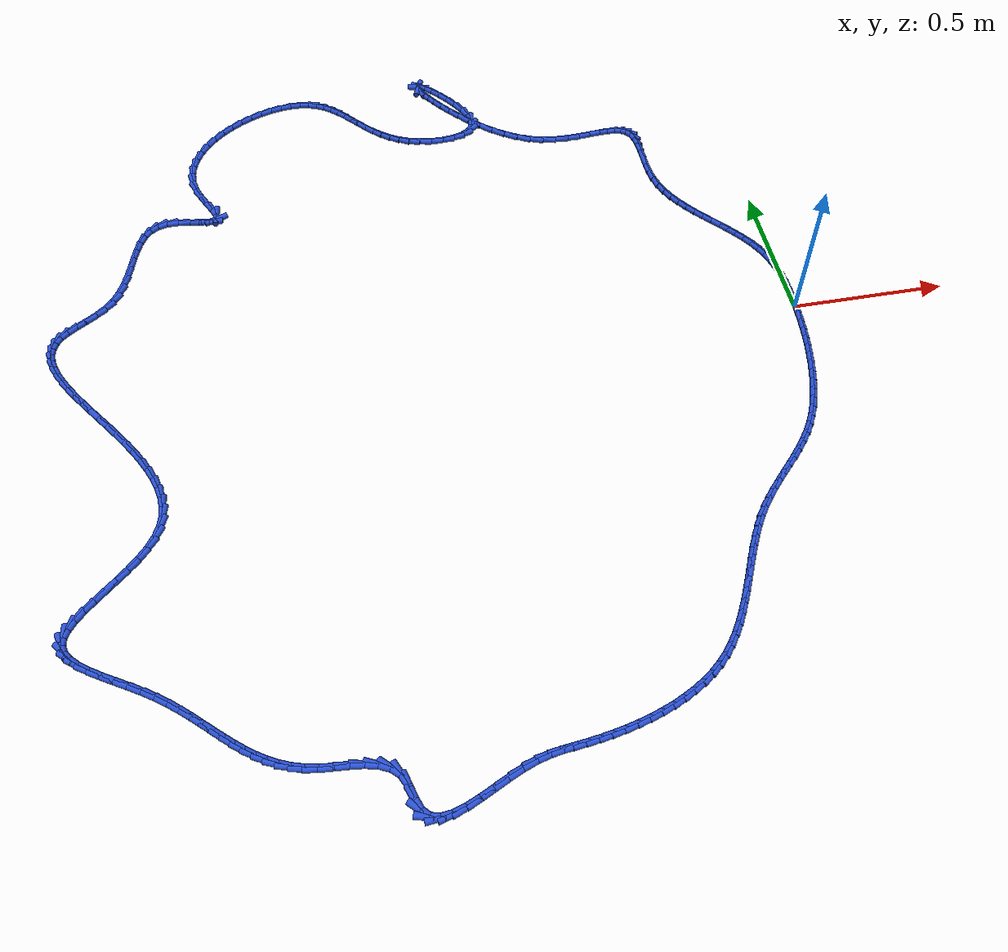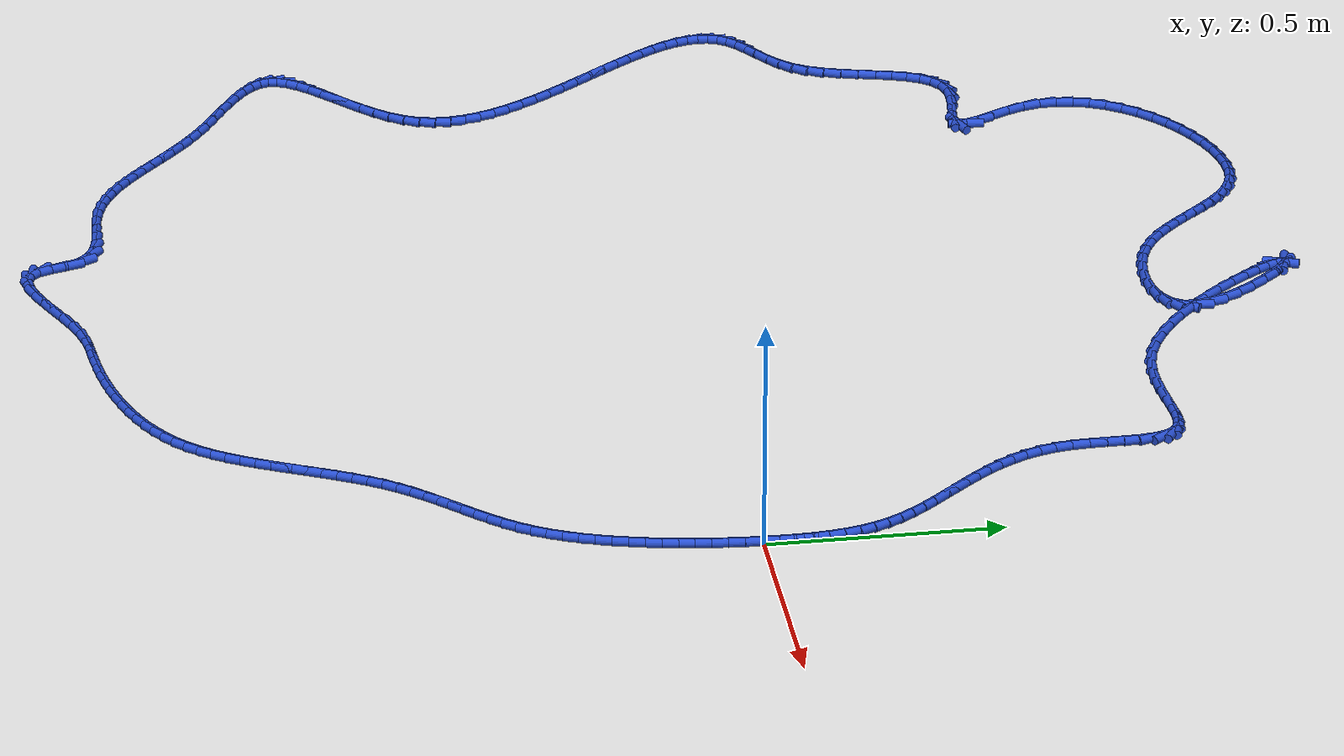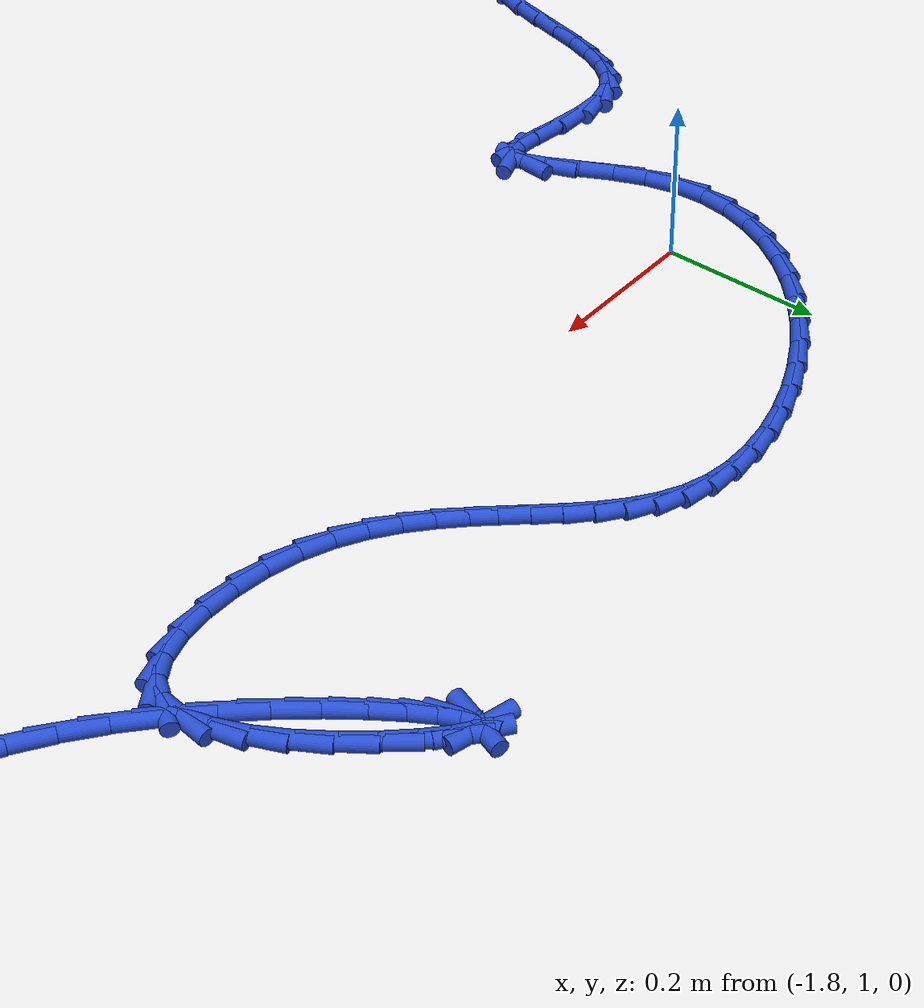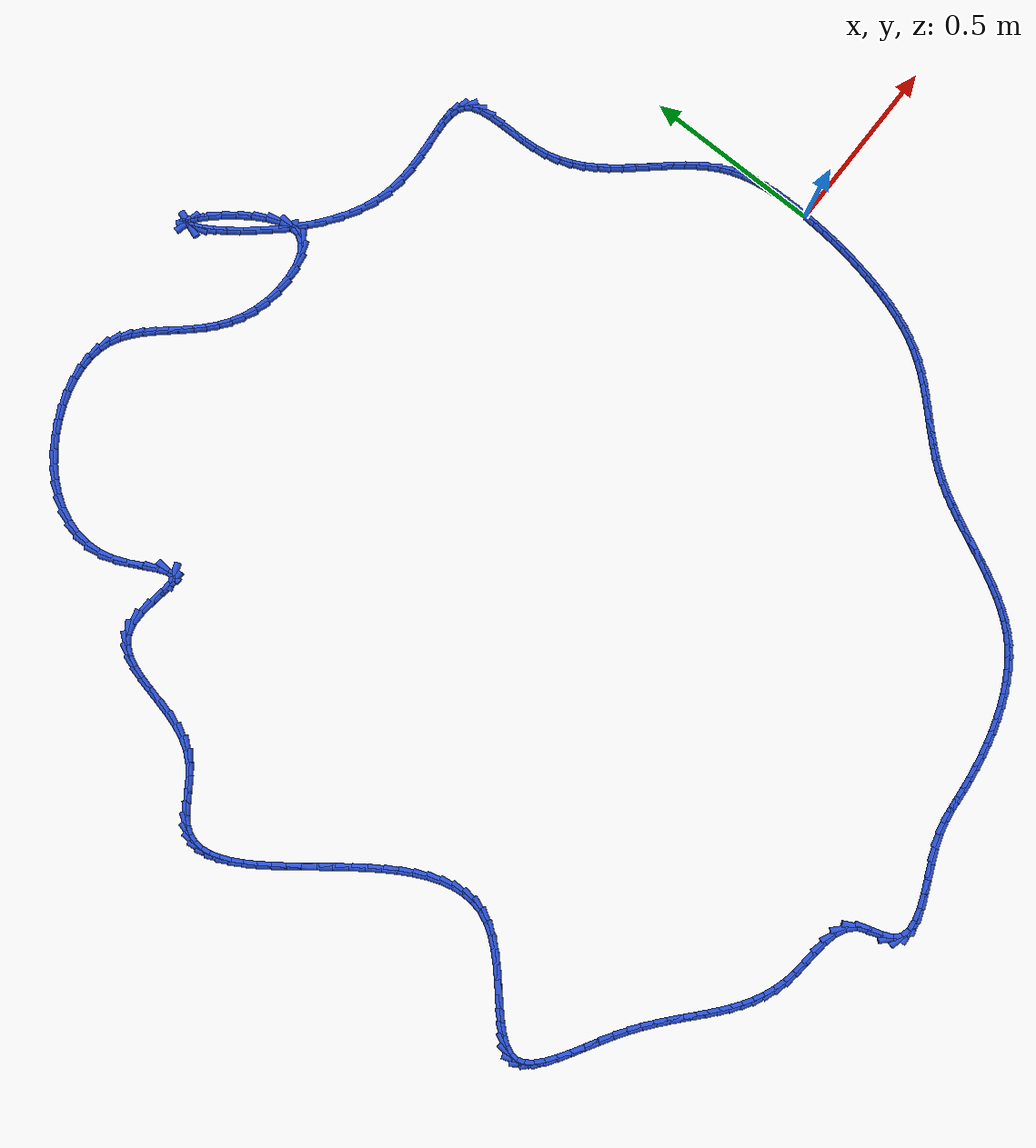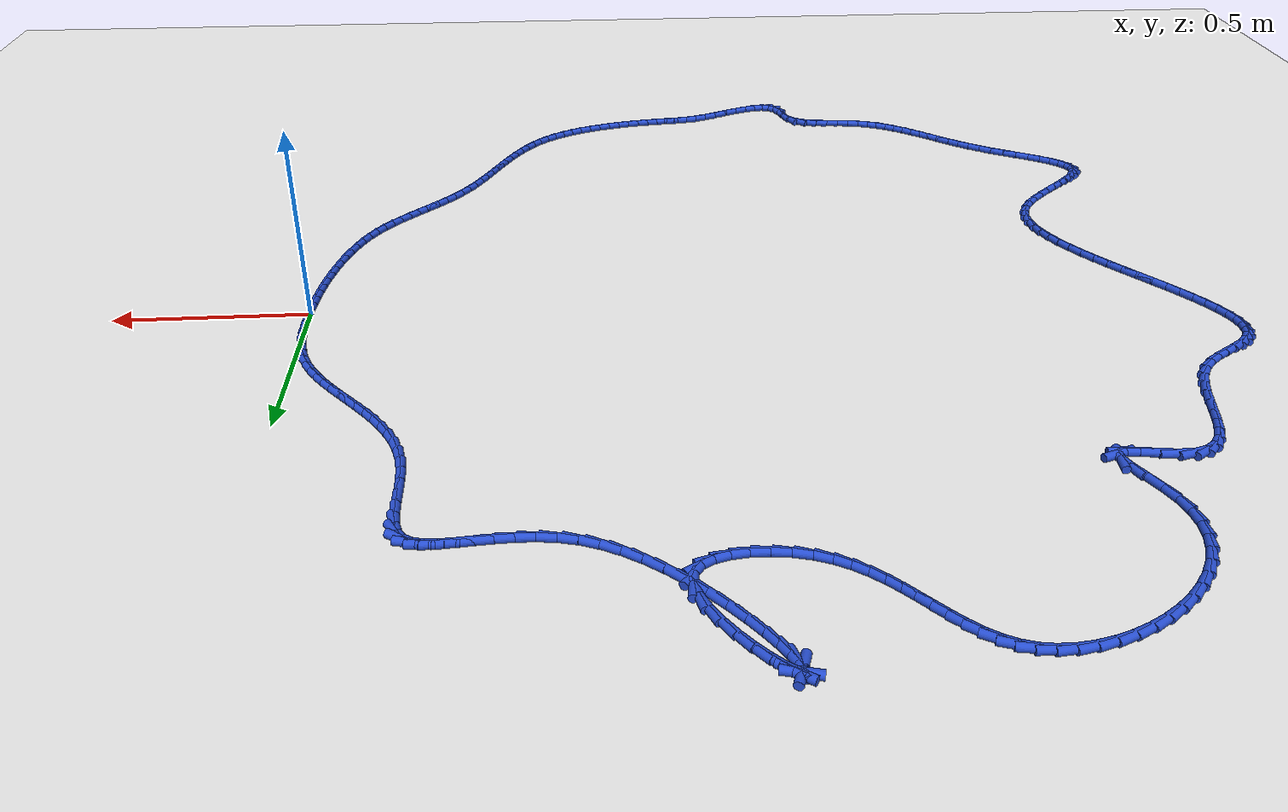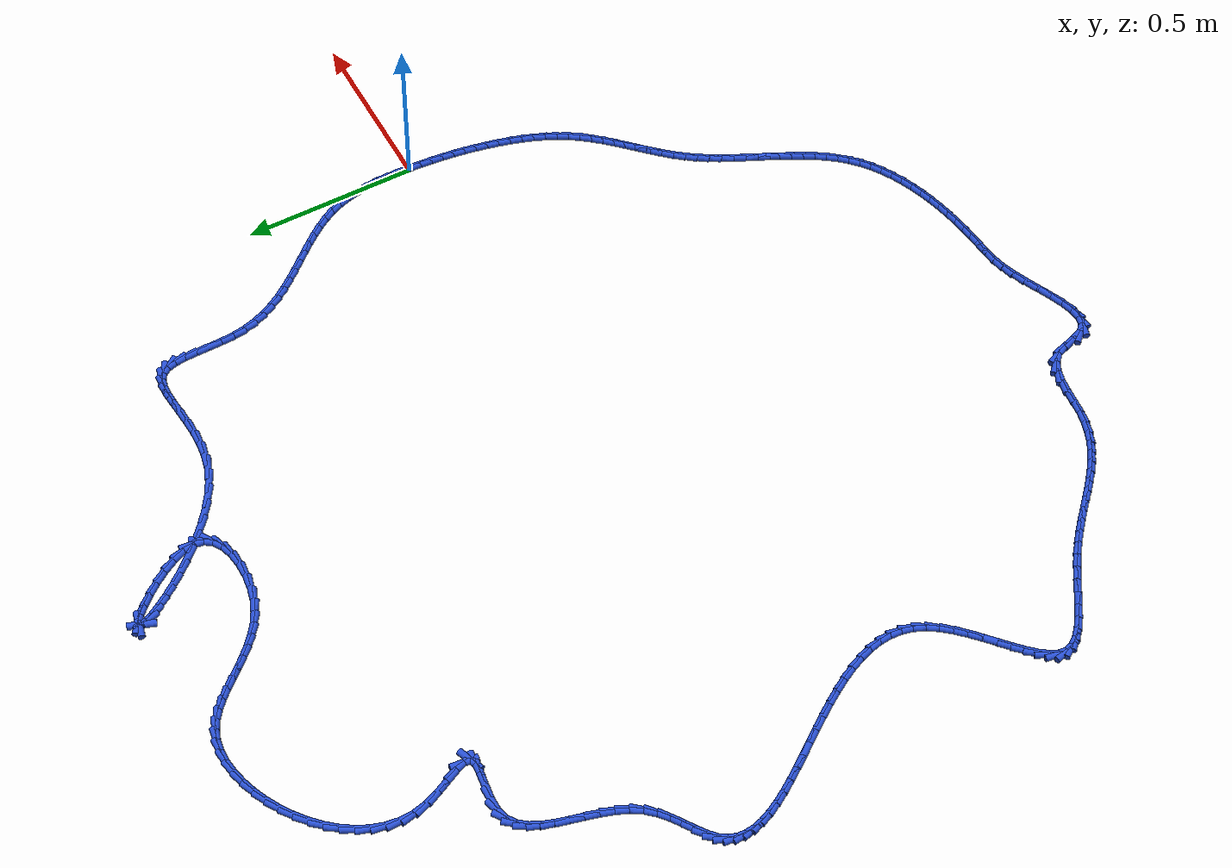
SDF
<sdf version="1.6">
 <world name="default">
  <light name="sun" type="directional">
   <pose>0 0 10 0 -0 0</pose>
   <diffuse>0.8 0.8 0.8 1</diffuse>
   <specular>0.2 0.2 0.2 1</specular>
   <attenuation>
    <range>1000</range>
    <constant>0.9</constant>
    <linear>0.01</linear>
    <quadratic>0.001</quadratic>
   </attenuation>
   <direction>-0.5 0.1 -0.9</direction>
  </light>
  <model name="ground_plane">
   <static>1</static>
   <link name="link">
    <collision name="collision">
     <geometry><plane><normal>0 0 1</normal><size>100 100</size></plane></geometry>
     <surface><friction><ode><mu>100</mu><mu2>50</mu2></ode></friction></surface>
    </collision>
    <visual name="visual">
     <cast_shadows>0</cast_shadows>
     <geometry><plane><normal>0 0 1</normal><size>100 100</size></plane></geometry>
     <material>
      <script><uri>file://media/materials/scripts/gazebo.material</uri><name>Gazebo/WhiteGlow</name></script>
     </material>
    </visual>
   </link>
  </model>
  <gravity>0 0 -9.8</gravity>
  <magnetic_field>6e-06 2.3e-05 -4.2e-05</magnetic_field>
  <atmosphere type="adiabatic"/>
  <physics name="default_physics" default="0" type="ode">
   <max_step_size>0.001</max_step_size>
   <real_time_factor>1</real_time_factor>
   <real_time_update_rate>1000</real_time_update_rate>
  </physics>
  <scene><ambient>0.4 0.4 0.4 1</ambient><background>0.7 0.7 0.7 1</background><shadows>1</shadows></scene>
  <spherical_coordinates>
   <surface_model>EARTH_WGS84</surface_model>
   <latitude_deg>0</latitude_deg>
   <longitude_deg>0</longitude_deg>
   <elevation>0</elevation>
   <heading_deg>0</heading_deg>
  </spherical_coordinates>
  <model name="line">
   <link name="link_0">
    <pose>-2.3960868011929648e-17 1.3877787807814457e-17 0.01 0 1.57 1.545897107826998</pose>
    <collision name="collision">
     <geometry><cylinder><radius>0.01</radius><length>0.08</length></cylinder></geometry>
    </collision>
    <visual name="visual">
     <material>
      <script><name>Gazebo/Blue</name><uri>file://media/materials/scripts/gazebo.material</uri></script>
     </material>
     <geometry><cylinder><radius>0.01</radius><length>0.08</length></cylinder></geometry>
    </visual>
   </link>
   <link name="link_1">
    <pose>0.0008592763216469214 0.03450303963018791 0.01 0 1.57 -1.5659385153599021</pose>
    <collision name="collision">
     <geometry><cylinder><radius>0.01</radius><length>0.08</length></cylinder></geometry>
    </collision>
    <visual name="visual">
     <material>
      <script><name>Gazebo/Blue</name><uri>file://media/materials/scripts/gazebo.material</uri></script>
     </material>
     <geometry><cylinder><radius>0.01</radius><length>0.08</length></cylinder></geometry>
    </visual>
   </link>
   <link name="link_2">
    <pose>0.0006910396736926901 0.06913495707600271 0.01 0 1.57 -1.5264834480917824</pose>
    <collision name="collision">
     <geometry><cylinder><radius>0.01</radius><length>0.08</length></cylinder></geometry>
    </collision>
    <visual name="visual">
     <material>
      <script><name>Gazebo/Blue</name><uri>file://media/materials/scripts/gazebo.material</uri></script>
     </material>
     <geometry><cylinder><radius>0.01</radius><length>0.08</length></cylinder></geometry>
    </visual>
   </link>
   <link name="link_3">
    <pose>-0.0008382564287101673 0.1036236886790465 0.01 0 1.57 -1.4764610011493455</pose>
    <collision name="collision">
     <geometry><cylinder><radius>0.01</radius><length>0.08</length></cylinder></geometry>
    </collision>
    <visual name="visual">
     <material>
      <script><name>Gazebo/Blue</name><uri>file://media/materials/scripts/gazebo.material</uri></script>
     </material>
     <geometry><cylinder><radius>0.01</radius><length>0.08</length></cylinder></geometry>
    </visual>
   </link>
   <link name="link_4">
    <pose>-0.0040621584704091055 0.13769717078092136 0.01 0 1.57 -1.4147627865338976</pose>
    <collision name="collision">
     <geometry><cylinder><radius>0.01</radius><length>0.08</length></cylinder></geometry>
    </collision>
    <visual name="visual">
     <material>
      <script><name>Gazebo/Blue</name><uri>file://media/materials/scripts/gazebo.material</uri></script>
     </material>
     <geometry><cylinder><radius>0.01</radius><length>0.08</length></cylinder></geometry>
    </visual>
   </link>
   <link name="link_5">
    <pose>-0.009314212936251573 0.1710833397232294 0.01 0 1.57 -1.3401755859879203</pose>
    <collision name="collision">
     <geometry><cylinder><radius>0.01</radius><length>0.08</length></cylinder></geometry>
    </collision>
    <visual name="visual">
     <material>
      <script><name>Gazebo/Blue</name><uri>file://media/materials/scripts/gazebo.material</uri></script>
     </material>
     <geometry><cylinder><radius>0.01</radius><length>0.08</length></cylinder></geometry>
    </visual>
   </link>
   <link name="link_6">
    <pose>-0.016927966311085025 0.2035101318475726 0.01 0 1.57 -1.251628712929015</pose>
    <collision name="collision">
     <geometry><cylinder><radius>0.01</radius><length>0.08</length></cylinder></geometry>
    </collision>
    <visual name="visual">
     <material>
      <script><name>Gazebo/Blue</name><uri>file://media/materials/scripts/gazebo.material</uri></script>
     </material>
     <geometry><cylinder><radius>0.01</radius><length>0.08</length></cylinder></geometry>
    </visual>
   </link>
   <link name="link_7">
    <pose>-0.027236965079756904 0.23470548349555323 0.01 0 1.57 -1.1515240778708402</pose>
    <collision name="collision">
     <geometry><cylinder><radius>0.01</radius><length>0.08</length></cylinder></geometry>
    </collision>
    <visual name="visual">
     <material>
      <script><name>Gazebo/Blue</name><uri>file://media/materials/scripts/gazebo.material</uri></script>
     </material>
     <geometry><cylinder><radius>0.01</radius><length>0.08</length></cylinder></geometry>
    </visual>
   </link>
   <link name="link_8">
    <pose>-0.040494596979720736 0.26445112748032834 0.01 0 1.57 -1.059333888668543</pose>
    <collision name="collision">
     <geometry><cylinder><radius>0.01</radius><length>0.08</length></cylinder></geometry>
    </collision>
    <visual name="visual">
     <material>
      <script><name>Gazebo/Blue</name><uri>file://media/materials/scripts/gazebo.material</uri></script>
     </material>
     <geometry><cylinder><radius>0.01</radius><length>0.08</length></cylinder></geometry>
    </visual>
   </link>
   <link name="link_9">
    <pose>-0.056445630595688676 0.29287014321380417 0.01 0 1.57 -0.9838645484405297</pose>
    <collision name="collision">
     <geometry><cylinder><radius>0.01</radius><length>0.08</length></cylinder></geometry>
    </collision>
    <visual name="visual">
     <material>
      <script><name>Gazebo/Blue</name><uri>file://media/materials/scripts/gazebo.material</uri></script>
     </material>
     <geometry><cylinder><radius>0.01</radius><length>0.08</length></cylinder></geometry>
    </visual>
   </link>
   <link name="link_10">
    <pose>-0.07463597597987633 0.32021906887233503 0.01 0 1.57 -0.9255285605055884</pose>
    <collision name="collision">
     <geometry><cylinder><radius>0.01</radius><length>0.08</length></cylinder></geometry>
    </collision>
    <visual name="visual">
     <material>
      <script><name>Gazebo/Blue</name><uri>file://media/materials/scripts/gazebo.material</uri></script>
     </material>
     <geometry><cylinder><radius>0.01</radius><length>0.08</length></cylinder></geometry>
    </visual>
   </link>
   <link name="link_11">
    <pose>-0.09461108389730388 0.3467547508710066 0.01 0 1.57 -0.8839255645810842</pose>
    <collision name="collision">
     <geometry><cylinder><radius>0.01</radius><length>0.08</length></cylinder></geometry>
    </collision>
    <visual name="visual">
     <material>
      <script><name>Gazebo/Blue</name><uri>file://media/materials/scripts/gazebo.material</uri></script>
     </material>
     <geometry><cylinder><radius>0.01</radius><length>0.08</length></cylinder></geometry>
    </visual>
   </link>
   <link name="link_12">
    <pose>-0.11591640511299148 0.37273403562490415 0.01 0 1.57 -0.858371076571808</pose>
    <collision name="collision">
     <geometry><cylinder><radius>0.01</radius><length>0.08</length></cylinder></geometry>
    </collision>
    <visual name="visual">
     <material>
      <script><name>Gazebo/Blue</name><uri>file://media/materials/scripts/gazebo.material</uri></script>
     </material>
     <geometry><cylinder><radius>0.01</radius><length>0.08</length></cylinder></geometry>
    </visual>
   </link>
   <link name="link_13">
    <pose>-0.13809739039195926 0.398413769549113 0.01 0 1.57 -0.8482296161784035</pose>
    <collision name="collision">
     <geometry><cylinder><radius>0.01</radius><length>0.08</length></cylinder></geometry>
    </collision>
    <visual name="visual">
     <material>
      <script><name>Gazebo/Blue</name><uri>file://media/materials/scripts/gazebo.material</uri></script>
     </material>
     <geometry><cylinder><radius>0.01</radius><length>0.08</length></cylinder></geometry>
    </visual>
   </link>
   <link name="link_14">
    <pose>-0.16069949049922738 0.4240507990587185 0.01 0 1.57 -0.8530871768644122</pose>
    <collision name="collision">
     <geometry><cylinder><radius>0.01</radius><length>0.08</length></cylinder></geometry>
    </collision>
    <visual name="visual">
     <material>
      <script><name>Gazebo/Blue</name><uri>file://media/materials/scripts/gazebo.material</uri></script>
     </material>
     <geometry><cylinder><radius>0.01</radius><length>0.08</length></cylinder></geometry>
    </visual>
   </link>
   <link name="link_15">
    <pose>-0.18326815619981596 0.44990197056880615 0.01 0 1.57 -0.8728035918655589</pose>
    <collision name="collision">
     <geometry><cylinder><radius>0.01</radius><length>0.08</length></cylinder></geometry>
    </collision>
    <visual name="visual">
     <material>
      <script><name>Gazebo/Blue</name><uri>file://media/materials/scripts/gazebo.material</uri></script>
     </material>
     <geometry><cylinder><radius>0.01</radius><length>0.08</length></cylinder></geometry>
    </visual>
   </link>
   <link name="link_16">
    <pose>-0.20534883825874514 0.4762241304944612 0.01 0 1.57 -0.907470738422886</pose>
    <collision name="collision">
     <geometry><cylinder><radius>0.01</radius><length>0.08</length></cylinder></geometry>
    </collision>
    <visual name="visual">
     <material>
      <script><name>Gazebo/Blue</name><uri>file://media/materials/scripts/gazebo.material</uri></script>
     </material>
     <geometry><cylinder><radius>0.01</radius><length>0.08</length></cylinder></geometry>
    </visual>
   </link>
   <link name="link_17">
    <pose>-0.2264869874410351 0.503274125250769 0.01 0 1.57 -0.9572798244319597</pose>
    <collision name="collision">
     <geometry><cylinder><radius>0.01</radius><length>0.08</length></cylinder></geometry>
    </collision>
    <visual name="visual">
     <material>
      <script><name>Gazebo/Blue</name><uri>file://media/materials/scripts/gazebo.material</uri></script>
     </material>
     <geometry><cylinder><radius>0.01</radius><length>0.08</length></cylinder></geometry>
    </visual>
   </link>
   <link name="link_18">
    <pose>-0.24622805451170596 0.5313088012528148 0.01 0 1.57 -1.022286160329267</pose>
    <collision name="collision">
     <geometry><cylinder><radius>0.01</radius><length>0.08</length></cylinder></geometry>
    </collision>
    <visual name="visual">
     <material>
      <script><name>Gazebo/Blue</name><uri>file://media/materials/scripts/gazebo.material</uri></script>
     </material>
     <geometry><cylinder><radius>0.01</radius><length>0.08</length></cylinder></geometry>
    </visual>
   </link>
   <link name="link_19">
    <pose>-0.26411749023577796 0.5605850049156844 0.01 0 1.57 -1.1020674663469452</pose>
    <collision name="collision">
     <geometry><cylinder><radius>0.01</radius><length>0.08</length></cylinder></geometry>
    </collision>
    <visual name="visual">
     <material>
      <script><name>Gazebo/Blue</name><uri>file://media/materials/scripts/gazebo.material</uri></script>
     </material>
     <geometry><cylinder><radius>0.01</radius><length>0.08</length></cylinder></geometry>
    </visual>
   </link>
   <link name="link_20">
    <pose>-0.27970074537827105 0.5913595826544625 0.01 0 1.57 -1.1953191149022981</pose>
    <collision name="collision">
     <geometry><cylinder><radius>0.01</radius><length>0.08</length></cylinder></geometry>
    </collision>
    <visual name="visual">
     <material>
      <script><name>Gazebo/Blue</name><uri>file://media/materials/scripts/gazebo.material</uri></script>
     </material>
     <geometry><cylinder><radius>0.01</radius><length>0.08</length></cylinder></geometry>
    </visual>
   </link>
   <link name="link_21">
    <pose>-0.2925232707042056 0.6238893808842352 0.01 0 1.57 -1.2995193620674919</pose>
    <collision name="collision">
     <geometry><cylinder><radius>0.01</radius><length>0.08</length></cylinder></geometry>
    </collision>
    <visual name="visual">
     <material>
      <script><name>Gazebo/Blue</name><uri>file://media/materials/scripts/gazebo.material</uri></script>
     </material>
     <geometry><cylinder><radius>0.01</radius><length>0.08</length></cylinder></geometry>
    </visual>
   </link>
   <link name="link_22">
    <pose>-0.30213051697860155 0.6584312460200873 0.01 0 1.57 -1.4100146691483508</pose>
    <collision name="collision">
     <geometry><cylinder><radius>0.01</radius><length>0.08</length></cylinder></geometry>
    </collision>
    <visual name="visual">
     <material>
      <script><name>Gazebo/Blue</name><uri>file://media/materials/scripts/gazebo.material</uri></script>
     </material>
     <geometry><cylinder><radius>0.01</radius><length>0.08</length></cylinder></geometry>
    </visual>
   </link>
   <link name="link_23">
    <pose>-0.3080963227162937 0.6952159774258417 0.01 0 1.57 -1.4997063180696923</pose>
    <collision name="collision">
     <geometry><cylinder><radius>0.01</radius><length>0.08</length></cylinder></geometry>
    </collision>
    <visual name="visual">
     <material>
      <script><name>Gazebo/Blue</name><uri>file://media/materials/scripts/gazebo.material</uri></script>
     </material>
     <geometry><cylinder><radius>0.01</radius><length>0.08</length></cylinder></geometry>
    </visual>
   </link>
   <link name="link_24">
    <pose>-0.31083687575884517 0.733701480655925 0.01 0 1.57 -1.5477143105425735</pose>
    <collision name="collision">
     <geometry><cylinder><radius>0.01</radius><length>0.08</length></cylinder></geometry>
    </collision>
    <visual name="visual">
     <material>
      <script><name>Gazebo/Blue</name><uri>file://media/materials/scripts/gazebo.material</uri></script>
     </material>
     <geometry><cylinder><radius>0.01</radius><length>0.08</length></cylinder></geometry>
    </visual>
   </link>
   <link name="link_25">
    <pose>-0.3117316999992263 0.7724617566341369 0.01 0 1.57 -1.5579819994210853</pose>
    <collision name="collision">
     <geometry><cylinder><radius>0.01</radius><length>0.08</length></cylinder></geometry>
    </collision>
    <visual name="visual">
     <material>
      <script><name>Gazebo/Blue</name><uri>file://media/materials/scripts/gazebo.material</uri></script>
     </material>
     <geometry><cylinder><radius>0.01</radius><length>0.08</length></cylinder></geometry>
    </visual>
   </link>
   <link name="link_26">
    <pose>-0.31221304113187165 0.8100224316341413 0.01 0 1.57 -1.5278234976914895</pose>
    <collision name="collision">
     <geometry><cylinder><radius>0.01</radius><length>0.08</length></cylinder></geometry>
    </collision>
    <visual name="visual">
     <material>
      <script><name>Gazebo/Blue</name><uri>file://media/materials/scripts/gazebo.material</uri></script>
     </material>
     <geometry><cylinder><radius>0.01</radius><length>0.08</length></cylinder></geometry>
    </visual>
   </link>
   <link name="link_27">
    <pose>-0.31371314485121593 0.8449091319296029 0.01 0 1.57 -1.4429571897700708</pose>
    <collision name="collision">
     <geometry><cylinder><radius>0.01</radius><length>0.08</length></cylinder></geometry>
    </collision>
    <visual name="visual">
     <material>
      <script><name>Gazebo/Blue</name><uri>file://media/materials/scripts/gazebo.material</uri></script>
     </material>
     <geometry><cylinder><radius>0.01</radius><length>0.08</length></cylinder></geometry>
    </visual>
   </link>
   <link name="link_28">
    <pose>-0.31766425685169386 0.8756474837941864 0.01 0 1.57 -1.2684291036820492</pose>
    <collision name="collision">
     <geometry><cylinder><radius>0.01</radius><length>0.08</length></cylinder></geometry>
    </collision>
    <visual name="visual">
     <material>
      <script><name>Gazebo/Blue</name><uri>file://media/materials/scripts/gazebo.material</uri></script>
     </material>
     <geometry><cylinder><radius>0.01</radius><length>0.08</length></cylinder></geometry>
    </visual>
   </link>
   <link name="link_29">
    <pose>-0.32549862282774 0.900763113501556 0.01 0 1.57 -0.9441774064784049</pose>
    <collision name="collision">
     <geometry><cylinder><radius>0.01</radius><length>0.08</length></cylinder></geometry>
    </collision>
    <visual name="visual">
     <material>
      <script><name>Gazebo/Blue</name><uri>file://media/materials/scripts/gazebo.material</uri></script>
     </material>
     <geometry><cylinder><radius>0.01</radius><length>0.08</length></cylinder></geometry>
    </visual>
   </link>
   <link name="link_30">
    <pose>-0.33859656596574617 0.9188554707817513 0.01 0 1.57 -0.5353127438071704</pose>
    <collision name="collision">
     <geometry><cylinder><radius>0.01</radius><length>0.08</length></cylinder></geometry>
    </collision>
    <visual name="visual">
     <material>
      <script><name>Gazebo/Blue</name><uri>file://media/materials/scripts/gazebo.material</uri></script>
     </material>
     <geometry><cylinder><radius>0.01</radius><length>0.08</length></cylinder></geometry>
    </visual>
   </link>
   <link name="link_31">
    <pose>-0.3573260009029215 0.9299634485115581 0.01 0 1.57 -0.22589252579197075</pose>
    <collision name="collision">
     <geometry><cylinder><radius>0.01</radius><length>0.08</length></cylinder></geometry>
    </collision>
    <visual name="visual">
     <material>
      <script><name>Gazebo/Blue</name><uri>file://media/materials/scripts/gazebo.material</uri></script>
     </material>
     <geometry><cylinder><radius>0.01</radius><length>0.08</length></cylinder></geometry>
    </visual>
   </link>
   <link name="link_32">
    <pose>-0.38113418991144293 0.9354349237110244 0.01 0 1.57 -0.043452407957987015</pose>
    <collision name="collision">
     <geometry><cylinder><radius>0.01</radius><length>0.08</length></cylinder></geometry>
    </collision>
    <visual name="visual">
     <material>
      <script><name>Gazebo/Blue</name><uri>file://media/materials/scripts/gazebo.material</uri></script>
     </material>
     <geometry><cylinder><radius>0.01</radius><length>0.08</length></cylinder></geometry>
    </visual>
   </link>
   <link name="link_33">
    <pose>-0.409434875931818 0.9366654312081971 0.01 0 1.57 0.05010021698335467</pose>
    <collision name="collision">
     <geometry><cylinder><radius>0.01</radius><length>0.08</length></cylinder></geometry>
    </collision>
    <visual name="visual">
     <material>
      <script><name>Gazebo/Blue</name><uri>file://media/materials/scripts/gazebo.material</uri></script>
     </material>
     <geometry><cylinder><radius>0.01</radius><length>0.08</length></cylinder></geometry>
    </visual>
   </link>
   <link name="link_34">
    <pose>-0.4416418019045541 0.9350505058311243 0.01 0 1.57 0.08605460967609724</pose>
    <collision name="collision">
     <geometry><cylinder><radius>0.01</radius><length>0.08</length></cylinder></geometry>
    </collision>
    <visual name="visual">
     <material>
      <script><name>Gazebo/Blue</name><uri>file://media/materials/scripts/gazebo.material</uri></script>
     </material>
     <geometry><cylinder><radius>0.01</radius><length>0.08</length></cylinder></geometry>
    </visual>
   </link>
   <link name="link_35">
    <pose>-0.4771687107701588 0.9319856824078534 0.01 0 1.57 0.08134480170607795</pose>
    <collision name="collision">
     <geometry><cylinder><radius>0.01</radius><length>0.08</length></cylinder></geometry>
    </collision>
    <visual name="visual">
     <material>
      <script><name>Gazebo/Blue</name><uri>file://media/materials/scripts/gazebo.material</uri></script>
     </material>
     <geometry><cylinder><radius>0.01</radius><length>0.08</length></cylinder></geometry>
    </visual>
   </link>
   <link name="link_36">
    <pose>-0.5154293454691394 0.928866495766433 0.01 0 1.57 0.04397308267729125</pose>
    <collision name="collision">
     <geometry><cylinder><radius>0.01</radius><length>0.08</length></cylinder></geometry>
    </collision>
    <visual name="visual">
     <material>
      <script><name>Gazebo/Blue</name><uri>file://media/materials/scripts/gazebo.material</uri></script>
     </material>
     <geometry><cylinder><radius>0.01</radius><length>0.08</length></cylinder></geometry>
    </visual>
   </link>
   <link name="link_37">
    <pose>-0.5558374489420034 0.9270884807349098 0.01 0 1.57 -0.02283870274848913</pose>
    <collision name="collision">
     <geometry><cylinder><radius>0.01</radius><length>0.08</length></cylinder></geometry>
    </collision>
    <visual name="visual">
     <material>
      <script><name>Gazebo/Blue</name><uri>file://media/materials/scripts/gazebo.material</uri></script>
     </material>
     <geometry><cylinder><radius>0.01</radius><length>0.08</length></cylinder></geometry>
    </visual>
   </link>
   <link name="link_38">
    <pose>-0.5978067641292586 0.928047172141332 0.01 0 1.57 -0.11799672751825001</pose>
    <collision name="collision">
     <geometry><cylinder><radius>0.01</radius><length>0.08</length></cylinder></geometry>
    </collision>
    <visual name="visual">
     <material>
      <script><name>Gazebo/Blue</name><uri>file://media/materials/scripts/gazebo.material</uri></script>
     </material>
     <geometry><cylinder><radius>0.01</radius><length>0.08</length></cylinder></geometry>
    </visual>
   </link>
   <link name="link_39">
    <pose>-0.6407510339714122 0.9331381048137477 0.01 0 1.57 -0.24031368107714585</pose>
    <collision name="collision">
     <geometry><cylinder><radius>0.01</radius><length>0.08</length></cylinder></geometry>
    </collision>
    <visual name="visual">
     <material>
      <script><name>Gazebo/Blue</name><uri>file://media/materials/scripts/gazebo.material</uri></script>
     </material>
     <geometry><cylinder><radius>0.01</radius><length>0.08</length></cylinder></geometry>
    </visual>
   </link>
   <link name="link_40">
    <pose>-0.6840840014089713 0.9437568135802041 0.01 0 1.57 -0.3784812080881994</pose>
    <collision name="collision">
     <geometry><cylinder><radius>0.01</radius><length>0.08</length></cylinder></geometry>
    </collision>
    <visual name="visual">
     <material>
      <script><name>Gazebo/Blue</name><uri>file://media/materials/scripts/gazebo.material</uri></script>
     </material>
     <geometry><cylinder><radius>0.01</radius><length>0.08</length></cylinder></geometry>
    </visual>
   </link>
   <link name="link_41">
    <pose>-0.7272371026917992 0.9609167609133242 0.01 0 1.57 -0.49697059487971396</pose>
    <collision name="collision">
     <geometry><cylinder><radius>0.01</radius><length>0.08</length></cylinder></geometry>
    </collision>
    <visual name="visual">
     <material>
      <script><name>Gazebo/Blue</name><uri>file://media/materials/scripts/gazebo.material</uri></script>
     </material>
     <geometry><cylinder><radius>0.01</radius><length>0.08</length></cylinder></geometry>
    </visual>
   </link>
   <link name="link_42">
    <pose>-0.7697192656213465 0.9839580434361594 0.01 0 1.57 -0.5920745081669407</pose>
    <collision name="collision">
     <geometry><cylinder><radius>0.01</radius><length>0.08</length></cylinder></geometry>
    </collision>
    <visual name="visual">
     <material>
      <script><name>Gazebo/Blue</name><uri>file://media/materials/scripts/gazebo.material</uri></script>
     </material>
     <geometry><cylinder><radius>0.01</radius><length>0.08</length></cylinder></geometry>
    </visual>
   </link>
   <link name="link_43">
    <pose>-0.8110606268978519 1.011762769175438 0.01 0 1.57 -0.6695893870224425</pose>
    <collision name="collision">
     <geometry><cylinder><radius>0.01</radius><length>0.08</length></cylinder></geometry>
    </collision>
    <visual name="visual">
     <material>
      <script><name>Gazebo/Blue</name><uri>file://media/materials/scripts/gazebo.material</uri></script>
     </material>
     <geometry><cylinder><radius>0.01</radius><length>0.08</length></cylinder></geometry>
    </visual>
   </link>
   <link name="link_44">
    <pose>-0.8507913237565817 1.0432130346044073 0.01 0 1.57 -0.7341744516920327</pose>
    <collision name="collision">
     <geometry><cylinder><radius>0.01</radius><length>0.08</length></cylinder></geometry>
    </collision>
    <visual name="visual">
     <material>
      <script><name>Gazebo/Blue</name><uri>file://media/materials/scripts/gazebo.material</uri></script>
     </material>
     <geometry><cylinder><radius>0.01</radius><length>0.08</length></cylinder></geometry>
    </visual>
   </link>
   <link name="link_45">
    <pose>-0.8884414934328029 1.077190936196314 0.01 0 1.57 -0.789481912293412</pose>
    <collision name="collision">
     <geometry><cylinder><radius>0.01</radius><length>0.08</length></cylinder></geometry>
    </collision>
    <visual name="visual">
     <material>
      <script><name>Gazebo/Blue</name><uri>file://media/materials/scripts/gazebo.material</uri></script>
     </material>
     <geometry><cylinder><radius>0.01</radius><length>0.08</length></cylinder></geometry>
    </visual>
   </link>
   <link name="link_46">
    <pose>-0.9235412731617817 1.1125785704244047 0.01 0 1.57 -0.8384768016143008</pose>
    <collision name="collision">
     <geometry><cylinder><radius>0.01</radius><length>0.08</length></cylinder></geometry>
    </collision>
    <visual name="visual">
     <material>
      <script><name>Gazebo/Blue</name><uri>file://media/materials/scripts/gazebo.material</uri></script>
     </material>
     <geometry><cylinder><radius>0.01</radius><length>0.08</length></cylinder></geometry>
    </visual>
   </link>
   <link name="link_47">
    <pose>-0.9556208001787851 1.1482580337619273 0.01 0 1.57 -0.8838134425617956</pose>
    <collision name="collision">
     <geometry><cylinder><radius>0.01</radius><length>0.08</length></cylinder></geometry>
    </collision>
    <visual name="visual">
     <material>
      <script><name>Gazebo/Blue</name><uri>file://media/materials/scripts/gazebo.material</uri></script>
     </material>
     <geometry><cylinder><radius>0.01</radius><length>0.08</length></cylinder></geometry>
    </visual>
   </link>
   <link name="link_48">
    <pose>-0.984210211719079 1.1831114226821278 0.01 0 1.57 -0.928319417941898</pose>
    <collision name="collision">
     <geometry><cylinder><radius>0.01</radius><length>0.08</length></cylinder></geometry>
    </collision>
    <visual name="visual">
     <material>
      <script><name>Gazebo/Blue</name><uri>file://media/materials/scripts/gazebo.material</uri></script>
     </material>
     <geometry><cylinder><radius>0.01</radius><length>0.08</length></cylinder></geometry>
    </visual>
   </link>
   <link name="link_49">
    <pose>-1.0088396450179302 1.2160208336582534 0.01 0 1.57 -0.9758390444276765</pose>
    <collision name="collision">
     <geometry><cylinder><radius>0.01</radius><length>0.08</length></cylinder></geometry>
    </collision>
    <visual name="visual">
     <material>
      <script><name>Gazebo/Blue</name><uri>file://media/materials/scripts/gazebo.material</uri></script>
     </material>
     <geometry><cylinder><radius>0.01</radius><length>0.08</length></cylinder></geometry>
    </visual>
   </link>
   <link name="link_50">
    <pose>-1.0290392373106059 1.2458683631635514 0.01 0 1.57 -1.0332682072119705</pose>
    <collision name="collision">
     <geometry><cylinder><radius>0.01</radius><length>0.08</length></cylinder></geometry>
    </collision>
    <visual name="visual">
     <material>
      <script><name>Gazebo/Blue</name><uri>file://media/materials/scripts/gazebo.material</uri></script>
     </material>
     <geometry><cylinder><radius>0.01</radius><length>0.08</length></cylinder></geometry>
    </visual>
   </link>
   <link name="link_51">
    <pose>-1.0443391258323713 1.2715361076712686 0.01 0 1.57 -1.1172018160227448</pose>
    <collision name="collision">
     <geometry><cylinder><radius>0.01</radius><length>0.08</length></cylinder></geometry>
    </collision>
    <visual name="visual">
     <material>
      <script><name>Gazebo/Blue</name><uri>file://media/materials/scripts/gazebo.material</uri></script>
     </material>
     <geometry><cylinder><radius>0.01</radius><length>0.08</length></cylinder></geometry>
    </visual>
   </link>
   <link name="link_52">
    <pose>-1.0542694478184942 1.2919061636546518 0.01 0 1.57 -1.2856263800954082</pose>
    <collision name="collision">
     <geometry><cylinder><radius>0.01</radius><length>0.08</length></cylinder></geometry>
    </collision>
    <visual name="visual">
     <material>
      <script><name>Gazebo/Blue</name><uri>file://media/materials/scripts/gazebo.material</uri></script>
     </material>
     <geometry><cylinder><radius>0.01</radius><length>0.08</length></cylinder></geometry>
    </visual>
   </link>
   <link name="link_53">
    <pose>-1.0583603405042403 1.3058606275869478 0.01 0 1.57 1.238142314369494</pose>
    <collision name="collision">
     <geometry><cylinder><radius>0.01</radius><length>0.08</length></cylinder></geometry>
    </collision>
    <visual name="visual">
     <material>
      <script><name>Gazebo/Blue</name><uri>file://media/materials/scripts/gazebo.material</uri></script>
     </material>
     <geometry><cylinder><radius>0.01</radius><length>0.08</length></cylinder></geometry>
    </visual>
   </link>
   <link name="link_54">
    <pose>-1.0561419411248767 1.3122815959414038 0.01 0 1.57 -0.24299462795347448</pose>
    <collision name="collision">
     <geometry><cylinder><radius>0.01</radius><length>0.08</length></cylinder></geometry>
    </collision>
    <visual name="visual">
     <material>
      <script><name>Gazebo/Blue</name><uri>file://media/materials/scripts/gazebo.material</uri></script>
     </material>
     <geometry><cylinder><radius>0.01</radius><length>0.08</length></cylinder></geometry>
    </visual>
   </link>
   <link name="link_55">
    <pose>-1.04714438691567 1.3100511651912679 0.01 0 1.57 -0.6329410903399565</pose>
    <collision name="collision">
     <geometry><cylinder><radius>0.01</radius><length>0.08</length></cylinder></geometry>
    </collision>
    <visual name="visual">
     <material>
      <script><name>Gazebo/Blue</name><uri>file://media/materials/scripts/gazebo.material</uri></script>
     </material>
     <geometry><cylinder><radius>0.01</radius><length>0.08</length></cylinder></geometry>
    </visual>
   </link>
   <link name="link_56">
    <pose>-1.0311285962101349 1.298301516335245 0.01 0 1.57 -0.7547785060208769</pose>
    <collision name="collision">
     <geometry><cylinder><radius>0.01</radius><length>0.08</length></cylinder></geometry>
    </collision>
    <visual name="visual">
     <material>
      <script><name>Gazebo/Blue</name><uri>file://media/materials/scripts/gazebo.material</uri></script>
     </material>
     <geometry><cylinder><radius>0.01</radius><length>0.08</length></cylinder></geometry>
    </visual>
   </link>
   <link name="link_57">
    <pose>-1.0095809501927824 1.2780346176361002 0.01 0 1.57 -0.8264151021963211</pose>
    <collision name="collision">
     <geometry><cylinder><radius>0.01</radius><length>0.08</length></cylinder></geometry>
    </collision>
    <visual name="visual">
     <material>
      <script><name>Gazebo/Blue</name><uri>file://media/materials/scripts/gazebo.material</uri></script>
     </material>
     <geometry><cylinder><radius>0.01</radius><length>0.08</length></cylinder></geometry>
    </visual>
   </link>
   <link name="link_58">
    <pose>-0.9847690223698371 1.2510989716375733 0.01 0 1.57 -0.8883562099774703</pose>
    <collision name="collision">
     <geometry><cylinder><radius>0.01</radius><length>0.08</length></cylinder></geometry>
    </collision>
    <visual name="visual">
     <material>
      <script><name>Gazebo/Blue</name><uri>file://media/materials/scripts/gazebo.material</uri></script>
     </material>
     <geometry><cylinder><radius>0.01</radius><length>0.08</length></cylinder></geometry>
    </visual>
   </link>
   <link name="link_59">
    <pose>-0.958964242167385 1.2193472593273762 0.01 0 1.57 -0.9557215106294031</pose>
    <collision name="collision">
     <geometry><cylinder><radius>0.01</radius><length>0.08</length></cylinder></geometry>
    </collision>
    <visual name="visual">
     <material>
      <script><name>Gazebo/Blue</name><uri>file://media/materials/scripts/gazebo.material</uri></script>
     </material>
     <geometry><cylinder><radius>0.01</radius><length>0.08</length></cylinder></geometry>
    </visual>
   </link>
   <link name="link_60">
    <pose>-0.9344380390115125 1.1846321616932216 0.01 0 1.57 -1.0411028806708467</pose>
    <collision name="collision">
     <geometry><cylinder><radius>0.01</radius><length>0.08</length></cylinder></geometry>
    </collision>
    <visual name="visual">
     <material>
      <script><name>Gazebo/Blue</name><uri>file://media/materials/scripts/gazebo.material</uri></script>
     </material>
     <geometry><cylinder><radius>0.01</radius><length>0.08</length></cylinder></geometry>
    </visual>
   </link>
   <link name="link_61">
    <pose>-0.9134618423283051 1.1488063597228206 0.01 0 1.57 -1.1630464603140283</pose>
    <collision name="collision">
     <geometry><cylinder><radius>0.01</radius><length>0.08</length></cylinder></geometry>
    </collision>
    <visual name="visual">
     <material>
      <script><name>Gazebo/Blue</name><uri>file://media/materials/scripts/gazebo.material</uri></script>
     </material>
     <geometry><cylinder><radius>0.01</radius><length>0.08</length></cylinder></geometry>
    </visual>
   </link>
   <link name="link_62">
    <pose>-0.8983070815438486 1.1137225344038848 0.01 0 1.57 -1.3567640663782528</pose>
    <collision name="collision">
     <geometry><cylinder><radius>0.01</radius><length>0.08</length></cylinder></geometry>
    </collision>
    <visual name="visual">
     <material>
      <script><name>Gazebo/Blue</name><uri>file://media/materials/scripts/gazebo.material</uri></script>
     </material>
     <geometry><cylinder><radius>0.01</radius><length>0.08</length></cylinder></geometry>
    </visual>
   </link>
   <link name="link_63">
    <pose>-0.8912451860842298 1.0812333667241274 0.01 0 1.57 1.453570218956255</pose>
    <collision name="collision">
     <geometry><cylinder><radius>0.01</radius><length>0.08</length></cylinder></geometry>
    </collision>
    <visual name="visual">
     <material>
      <script><name>Gazebo/Blue</name><uri>file://media/materials/scripts/gazebo.material</uri></script>
     </material>
     <geometry><cylinder><radius>0.01</radius><length>0.08</length></cylinder></geometry>
    </visual>
   </link>
   <link name="link_64">
    <pose>-0.8945475626776275 1.0531915274551265 0.01 0 1.57 0.9723710007917653</pose>
    <collision name="collision">
     <geometry><cylinder><radius>0.01</radius><length>0.08</length></cylinder></geometry>
    </collision>
    <visual name="visual">
     <material>
      <script><name>Gazebo/Blue</name><uri>file://media/materials/scripts/gazebo.material</uri></script>
     </material>
     <geometry><cylinder><radius>0.01</radius><length>0.08</length></cylinder></geometry>
    </visual>
   </link>
   <link name="link_65">
    <pose>-0.9096333098303867 1.0310660707435844 0.01 0 1.57 0.5700020703874724</pose>
    <collision name="collision">
     <geometry><cylinder><radius>0.01</radius><length>0.08</length></cylinder></geometry>
    </collision>
    <visual name="visual">
     <material>
      <script><name>Gazebo/Blue</name><uri>file://media/materials/scripts/gazebo.material</uri></script>
     </material>
     <geometry><cylinder><radius>0.01</radius><length>0.08</length></cylinder></geometry>
    </visual>
   </link>
   <link name="link_66">
    <pose>-0.9348127047340459 1.014926796910443 0.01 0 1.57 0.30645260078980635</pose>
    <collision name="collision">
     <geometry><cylinder><radius>0.01</radius><length>0.08</length></cylinder></geometry>
    </collision>
    <visual name="visual">
     <material>
      <script><name>Gazebo/Blue</name><uri>file://media/materials/scripts/gazebo.material</uri></script>
     </material>
     <geometry><cylinder><radius>0.01</radius><length>0.08</length></cylinder></geometry>
    </visual>
   </link>
   <link name="link_67">
    <pose>-0.967687410351808 1.0045245650865335 0.01 0 1.57 0.12803854618821603</pose>
    <collision name="collision">
     <geometry><cylinder><radius>0.01</radius><length>0.08</length></cylinder></geometry>
    </collision>
    <visual name="visual">
     <material>
      <script><name>Gazebo/Blue</name><uri>file://media/materials/scripts/gazebo.material</uri></script>
     </material>
     <geometry><cylinder><radius>0.01</radius><length>0.08</length></cylinder></geometry>
    </visual>
   </link>
   <link name="link_68">
    <pose>-1.0058590896468733 0.999610234402685 0.01 0 1.57 -0.00789920485799322</pose>
    <collision name="collision">
     <geometry><cylinder><radius>0.01</radius><length>0.08</length></cylinder></geometry>
    </collision>
    <visual name="visual">
     <material>
      <script><name>Gazebo/Blue</name><uri>file://media/materials/scripts/gazebo.material</uri></script>
     </material>
     <geometry><cylinder><radius>0.01</radius><length>0.08</length></cylinder></geometry>
    </visual>
   </link>
   <link name="link_69">
    <pose>-1.046929405582444 0.999934663989729 0.01 0 1.57 -0.12714230599950918</pose>
    <collision name="collision">
     <geometry><cylinder><radius>0.01</radius><length>0.08</length></cylinder></geometry>
    </collision>
    <visual name="visual">
     <material>
      <script><name>Gazebo/Blue</name><uri>file://media/materials/scripts/gazebo.material</uri></script>
     </material>
     <geometry><cylinder><radius>0.01</radius><length>0.08</length></cylinder></geometry>
    </visual>
   </link>
   <link name="link_70">
    <pose>-1.0885000211217233 1.0052487129784953 0.01 0 1.57 -0.2482110267522975</pose>
    <collision name="collision">
     <geometry><cylinder><radius>0.01</radius><length>0.08</length></cylinder></geometry>
    </collision>
    <visual name="visual">
     <material>
      <script><name>Gazebo/Blue</name><uri>file://media/materials/scripts/gazebo.material</uri></script>
     </material>
     <geometry><cylinder><radius>0.01</radius><length>0.08</length></cylinder></geometry>
    </visual>
   </link>
   <link name="link_71">
    <pose>-1.1281726500950469 1.015303232024965 0.01 0 1.57 -0.3822972875821599</pose>
    <collision name="collision">
     <geometry><cylinder><radius>0.01</radius><length>0.08</length></cylinder></geometry>
    </collision>
    <visual name="visual">
     <material>
      <script><name>Gazebo/Blue</name><uri>file://media/materials/scripts/gazebo.material</uri></script>
     </material>
     <geometry><cylinder><radius>0.01</radius><length>0.08</length></cylinder></geometry>
    </visual>
   </link>
   <link name="link_72">
    <pose>-1.1641147867218438 1.0297548084962052 0.01 0 1.57 -0.5119892710026104</pose>
    <collision name="collision">
     <geometry><cylinder><radius>0.01</radius><length>0.08</length></cylinder></geometry>
    </collision>
    <visual name="visual">
     <material>
      <script><name>Gazebo/Blue</name><uri>file://media/materials/scripts/gazebo.material</uri></script>
     </material>
     <geometry><cylinder><radius>0.01</radius><length>0.08</length></cylinder></geometry>
    </visual>
   </link>
   <link name="link_73">
    <pose>-1.1964607025708682 1.0479323497882465 0.01 0 1.57 -0.6253092240364163</pose>
    <collision name="collision">
     <geometry><cylinder><radius>0.01</radius><length>0.08</length></cylinder></geometry>
    </collision>
    <visual name="visual">
     <material>
      <script><name>Gazebo/Blue</name><uri>file://media/materials/scripts/gazebo.material</uri></script>
     </material>
     <geometry><cylinder><radius>0.01</radius><length>0.08</length></cylinder></geometry>
    </visual>
   </link>
   <link name="link_74">
    <pose>-1.225771760342248 1.0690936066867371 0.01 0 1.57 -0.7171361642608705</pose>
    <collision name="collision">
     <geometry><cylinder><radius>0.01</radius><length>0.08</length></cylinder></geometry>
    </collision>
    <visual name="visual">
     <material>
      <script><name>Gazebo/Blue</name><uri>file://media/materials/scripts/gazebo.material</uri></script>
     </material>
     <geometry><cylinder><radius>0.01</radius><length>0.08</length></cylinder></geometry>
    </visual>
   </link>
   <link name="link_75">
    <pose>-1.25260932273611 1.0924963299773243 0.01 0 1.57 -0.7849267508723177</pose>
    <collision name="collision">
     <geometry><cylinder><radius>0.01</radius><length>0.08</length></cylinder></geometry>
    </collision>
    <visual name="visual">
     <material>
      <script><name>Gazebo/Blue</name><uri>file://media/materials/scripts/gazebo.material</uri></script>
     </material>
     <geometry><cylinder><radius>0.01</radius><length>0.08</length></cylinder></geometry>
    </visual>
   </link>
   <link name="link_76">
    <pose>-1.2775347524525806 1.1173982704456555 0.01 0 1.57 -0.8277067956092622</pose>
    <collision name="collision">
     <geometry><cylinder><radius>0.01</radius><length>0.08</length></cylinder></geometry>
    </collision>
    <visual name="visual">
     <material>
      <script><name>Gazebo/Blue</name><uri>file://media/materials/scripts/gazebo.material</uri></script>
     </material>
     <geometry><cylinder><radius>0.01</radius><length>0.08</length></cylinder></geometry>
    </visual>
   </link>
   <link name="link_77">
    <pose>-1.3011094121917877 1.1430571788773782 0.01 0 1.57 -0.8449323806353404</pose>
    <collision name="collision">
     <geometry><cylinder><radius>0.01</radius><length>0.08</length></cylinder></geometry>
    </collision>
    <visual name="visual">
     <material>
      <script><name>Gazebo/Blue</name><uri>file://media/materials/scripts/gazebo.material</uri></script>
     </material>
     <geometry><cylinder><radius>0.01</radius><length>0.08</length></cylinder></geometry>
    </visual>
   </link>
   <link name="link_78">
    <pose>-1.3238946646538583 1.16873080605814 0.01 0 1.57 -0.8356447323193349</pose>
    <collision name="collision">
     <geometry><cylinder><radius>0.01</radius><length>0.08</length></cylinder></geometry>
    </collision>
    <visual name="visual">
     <material>
      <script><name>Gazebo/Blue</name><uri>file://media/materials/scripts/gazebo.material</uri></script>
     </material>
     <geometry><cylinder><radius>0.01</radius><length>0.08</length></cylinder></geometry>
    </visual>
   </link>
   <link name="link_79">
    <pose>-1.3464518725389194 1.193676902773588 0.01 0 1.57 -0.7980313259196378</pose>
    <collision name="collision">
     <geometry><cylinder><radius>0.01</radius><length>0.08</length></cylinder></geometry>
    </collision>
    <visual name="visual">
     <material>
      <script><name>Gazebo/Blue</name><uri>file://media/materials/scripts/gazebo.material</uri></script>
     </material>
     <geometry><cylinder><radius>0.01</radius><length>0.08</length></cylinder></geometry>
    </visual>
   </link>
   <link name="link_80">
    <pose>-1.369342398547098 1.2171532198093704 0.01 0 1.57 -0.7294975968443765</pose>
    <collision name="collision">
     <geometry><cylinder><radius>0.01</radius><length>0.08</length></cylinder></geometry>
    </collision>
    <visual name="visual">
     <material>
      <script><name>Gazebo/Blue</name><uri>file://media/materials/scripts/gazebo.material</uri></script>
     </material>
     <geometry><cylinder><radius>0.01</radius><length>0.08</length></cylinder></geometry>
    </visual>
   </link>
   <link name="link_81">
    <pose>-1.393127605378521 1.2384175079511337 0.01 0 1.57 -0.6275705124526488</pose>
    <collision name="collision">
     <geometry><cylinder><radius>0.01</radius><length>0.08</length></cylinder></geometry>
    </collision>
    <visual name="visual">
     <material>
      <script><name>Gazebo/Blue</name><uri>file://media/materials/scripts/gazebo.material</uri></script>
     </material>
     <geometry><cylinder><radius>0.01</radius><length>0.08</length></cylinder></geometry>
    </visual>
   </link>
   <link name="link_82">
    <pose>-1.4183688557333165 1.2567275179845263 0.01 0 1.57 -0.49211216224122334</pose>
    <collision name="collision">
     <geometry><cylinder><radius>0.01</radius><length>0.08</length></cylinder></geometry>
    </collision>
    <visual name="visual">
     <material>
      <script><name>Gazebo/Blue</name><uri>file://media/materials/scripts/gazebo.material</uri></script>
     </material>
     <geometry><cylinder><radius>0.01</radius><length>0.08</length></cylinder></geometry>
    </visual>
   </link>
   <link name="link_83">
    <pose>-1.4456275123116111 1.271341000695195 0.01 0 1.57 -0.32864731974328726</pose>
    <collision name="collision">
     <geometry><cylinder><radius>0.01</radius><length>0.08</length></cylinder></geometry>
    </collision>
    <visual name="visual">
     <material>
      <script><name>Gazebo/Blue</name><uri>file://media/materials/scripts/gazebo.material</uri></script>
     </material>
     <geometry><cylinder><radius>0.01</radius><length>0.08</length></cylinder></geometry>
    </visual>
   </link>
   <link name="link_84">
    <pose>-1.4754646967463991 1.2815159038398565 0.01 0 1.57 -0.15827107035254795</pose>
    <collision name="collision">
     <geometry><cylinder><radius>0.01</radius><length>0.08</length></cylinder></geometry>
    </collision>
    <visual name="visual">
     <material>
      <script><name>Gazebo/Blue</name><uri>file://media/materials/scripts/gazebo.material</uri></script>
     </material>
     <geometry><cylinder><radius>0.01</radius><length>0.08</length></cylinder></geometry>
    </visual>
   </link>
   <link name="link_85">
    <pose>-1.5081660796076852 1.286735240656524 0.01 0 1.57 -0.011544589115216462</pose>
    <collision name="collision">
     <geometry><cylinder><radius>0.01</radius><length>0.08</length></cylinder></geometry>
    </collision>
    <visual name="visual">
     <material>
      <script><name>Gazebo/Blue</name><uri>file://media/materials/scripts/gazebo.material</uri></script>
     </material>
     <geometry><cylinder><radius>0.01</radius><length>0.08</length></cylinder></geometry>
    </visual>
   </link>
   <link name="link_86">
    <pose>-1.5432122353537963 1.2871398521000461 0.01 0 1.57 0.11251674956214293</pose>
    <collision name="collision">
     <geometry><cylinder><radius>0.01</radius><length>0.08</length></cylinder></geometry>
    </collision>
    <visual name="visual">
     <material>
      <script><name>Gazebo/Blue</name><uri>file://media/materials/scripts/gazebo.material</uri></script>
     </material>
     <geometry><cylinder><radius>0.01</radius><length>0.08</length></cylinder></geometry>
    </visual>
   </link>
   <link name="link_87">
    <pose>-1.579937428418122 1.2829901260815368 0.01 0 1.57 0.22011646677106772</pose>
    <collision name="collision">
     <geometry><cylinder><radius>0.01</radius><length>0.08</length></cylinder></geometry>
    </collision>
    <visual name="visual">
     <material>
      <script><name>Gazebo/Blue</name><uri>file://media/materials/scripts/gazebo.material</uri></script>
     </material>
     <geometry><cylinder><radius>0.01</radius><length>0.08</length></cylinder></geometry>
    </visual>
   </link>
   <link name="link_88">
    <pose>-1.617675923234053 1.2745464505121102 0.01 0 1.57 0.31658748666275205</pose>
    <collision name="collision">
     <geometry><cylinder><radius>0.01</radius><length>0.08</length></cylinder></geometry>
    </collision>
    <visual name="visual">
     <material>
      <script><name>Gazebo/Blue</name><uri>file://media/materials/scripts/gazebo.material</uri></script>
     </material>
     <geometry><cylinder><radius>0.01</radius><length>0.08</length></cylinder></geometry>
    </visual>
   </link>
   <link name="link_89">
    <pose>-1.6557619842349802 1.2620692133028801 0.01 0 1.57 0.40632635485857166</pose>
    <collision name="collision">
     <geometry><cylinder><radius>0.01</radius><length>0.08</length></cylinder></geometry>
    </collision>
    <visual name="visual">
     <material>
      <script><name>Gazebo/Blue</name><uri>file://media/materials/scripts/gazebo.material</uri></script>
     </material>
     <geometry><cylinder><radius>0.01</radius><length>0.08</length></cylinder></geometry>
    </visual>
   </link>
   <link name="link_90">
    <pose>-1.6935298758542943 1.245818802364961 0.01 0 1.57 0.49302276827547603</pose>
    <collision name="collision">
     <geometry><cylinder><radius>0.01</radius><length>0.08</length></cylinder></geometry>
    </collision>
    <visual name="visual">
     <material>
      <script><name>Gazebo/Blue</name><uri>file://media/materials/scripts/gazebo.material</uri></script>
     </material>
     <geometry><cylinder><radius>0.01</radius><length>0.08</length></cylinder></geometry>
    </visual>
   </link>
   <link name="link_91">
    <pose>-1.7303138625253864 1.2260556056094667 0.01 0 1.57 0.5799338741252384</pose>
    <collision name="collision">
     <geometry><cylinder><radius>0.01</radius><length>0.08</length></cylinder></geometry>
    </collision>
    <visual name="visual">
     <material>
      <script><name>Gazebo/Blue</name><uri>file://media/materials/scripts/gazebo.material</uri></script>
     </material>
     <geometry><cylinder><radius>0.01</radius><length>0.08</length></cylinder></geometry>
    </visual>
   </link>
   <link name="link_92">
    <pose>-1.7654482086816468 1.2030400109475112 0.01 0 1.57 0.6701242635236726</pose>
    <collision name="collision">
     <geometry><cylinder><radius>0.01</radius><length>0.08</length></cylinder></geometry>
    </collision>
    <visual name="visual">
     <material>
      <script><name>Gazebo/Blue</name><uri>file://media/materials/scripts/gazebo.material</uri></script>
     </material>
     <geometry><cylinder><radius>0.01</radius><length>0.08</length></cylinder></geometry>
    </visual>
   </link>
   <link name="link_93">
    <pose>-1.7982671787564655 1.1770324062902096 0.01 0 1.57 0.7666450470489968</pose>
    <collision name="collision">
     <geometry><cylinder><radius>0.01</radius><length>0.08</length></cylinder></geometry>
    </collision>
    <visual name="visual">
     <material>
      <script><name>Gazebo/Blue</name><uri>file://media/materials/scripts/gazebo.material</uri></script>
     </material>
     <geometry><cylinder><radius>0.01</radius><length>0.08</length></cylinder></geometry>
    </visual>
   </link>
   <link name="link_94">
    <pose>-1.8281050371832348 1.1482931795486748 0.01 0 1.57 0.8726209131466792</pose>
    <collision name="collision">
     <geometry><cylinder><radius>0.01</radius><length>0.08</length></cylinder></geometry>
    </collision>
    <visual name="visual">
     <material>
      <script><name>Gazebo/Blue</name><uri>file://media/materials/scripts/gazebo.material</uri></script>
     </material>
     <geometry><cylinder><radius>0.01</radius><length>0.08</length></cylinder></geometry>
    </visual>
   </link>
   <link name="link_95">
    <pose>-1.8542960483953443 1.117082718634022 0.01 0 1.57 0.9911765468494342</pose>
    <collision name="collision">
     <geometry><cylinder><radius>0.01</radius><length>0.08</length></cylinder></geometry>
    </collision>
    <visual name="visual">
     <material>
      <script><name>Gazebo/Blue</name><uri>file://media/materials/scripts/gazebo.material</uri></script>
     </material>
     <geometry><cylinder><radius>0.01</radius><length>0.08</length></cylinder></geometry>
    </visual>
   </link>
   <link name="link_96">
    <pose>-1.876174476826184 1.0836614114573646 0.01 0 1.57 1.1250778789288784</pose>
    <collision name="collision">
     <geometry><cylinder><radius>0.01</radius><length>0.08</length></cylinder></geometry>
    </collision>
    <visual name="visual">
     <material>
      <script><name>Gazebo/Blue</name><uri>file://media/materials/scripts/gazebo.material</uri></script>
     </material>
     <geometry><cylinder><radius>0.01</radius><length>0.08</length></cylinder></geometry>
    </visual>
   </link>
   <link name="link_97">
    <pose>-1.8930745869091465 1.0482896459298172 0.01 0 1.57 1.2759392002402123</pose>
    <collision name="collision">
     <geometry><cylinder><radius>0.01</radius><length>0.08</length></cylinder></geometry>
    </collision>
    <visual name="visual">
     <material>
      <script><name>Gazebo/Blue</name><uri>file://media/materials/scripts/gazebo.material</uri></script>
     </material>
     <geometry><cylinder><radius>0.01</radius><length>0.08</length></cylinder></geometry>
    </visual>
   </link>
   <link name="link_98">
    <pose>-1.9043306430776215 1.0112278099624936 0.01 0 1.57 1.4429939524366753</pose>
    <collision name="collision">
     <geometry><cylinder><radius>0.01</radius><length>0.08</length></cylinder></geometry>
    </collision>
    <visual name="visual">
     <material>
      <script><name>Gazebo/Blue</name><uri>file://media/materials/scripts/gazebo.material</uri></script>
     </material>
     <geometry><cylinder><radius>0.01</radius><length>0.08</length></cylinder></geometry>
    </visual>
   </link>
   <link name="link_99">
    <pose>-1.909276909764999 0.9727362914665074 0.01 0 1.57 -1.5196755810153033</pose>
    <collision name="collision">
     <geometry><cylinder><radius>0.01</radius><length>0.08</length></cylinder></geometry>
    </collision>
    <visual name="visual">
     <material>
      <script><name>Gazebo/Blue</name><uri>file://media/materials/scripts/gazebo.material</uri></script>
     </material>
     <geometry><cylinder><radius>0.01</radius><length>0.08</length></cylinder></geometry>
    </visual>
   </link>
   <link name="link_100">
    <pose>-1.9072476514046706 0.933075478352974 0.01 0 1.57 -1.3367968789407314</pose>
    <collision name="collision">
     <geometry><cylinder><radius>0.01</radius><length>0.08</length></cylinder></geometry>
    </collision>
    <visual name="visual">
     <material>
      <script><name>Gazebo/Blue</name><uri>file://media/materials/scripts/gazebo.material</uri></script>
     </material>
     <geometry><cylinder><radius>0.01</radius><length>0.08</length></cylinder></geometry>
    </visual>
   </link>
   <link name="link_101">
    <pose>-1.8975772153934296 0.8925057913400672 0.01 0 1.57 -1.178196642931788</pose>
    <collision name="collision">
     <geometry><cylinder><radius>0.01</radius><length>0.08</length></cylinder></geometry>
    </collision>
    <visual name="visual">
     <material>
      <script><name>Gazebo/Blue</name><uri>file://media/materials/scripts/gazebo.material</uri></script>
     </material>
     <geometry><cylinder><radius>0.01</radius><length>0.08</length></cylinder></geometry>
    </visual>
   </link>
   <link name="link_102">
    <pose>-1.8806868896258846 0.8517174710618585 0.01 0 1.57 -1.097393142828479</pose>
    <collision name="collision">
     <geometry><cylinder><radius>0.01</radius><length>0.08</length></cylinder></geometry>
    </collision>
    <visual name="visual">
     <material>
      <script><name>Gazebo/Blue</name><uri>file://media/materials/scripts/gazebo.material</uri></script>
     </material>
     <geometry><cylinder><radius>0.01</radius><length>0.08</length></cylinder></geometry>
    </visual>
   </link>
   <link name="link_103">
    <pose>-1.8608058067159037 0.8129065328477847 0.01 0 1.57 -1.0919846308844898</pose>
    <collision name="collision">
     <geometry><cylinder><radius>0.01</radius><length>0.08</length></cylinder></geometry>
    </collision>
    <visual name="visual">
     <material>
      <script><name>Gazebo/Blue</name><uri>file://media/materials/scripts/gazebo.material</uri></script>
     </material>
     <geometry><cylinder><radius>0.01</radius><length>0.08</length></cylinder></geometry>
    </visual>
   </link>
   <link name="link_104">
    <pose>-1.8429964822360807 0.7785985451113286 0.01 0 1.57 -1.1977934822368042</pose>
    <collision name="collision">
     <geometry><cylinder><radius>0.01</radius><length>0.08</length></cylinder></geometry>
    </collision>
    <visual name="visual">
     <material>
      <script><name>Gazebo/Blue</name><uri>file://media/materials/scripts/gazebo.material</uri></script>
     </material>
     <geometry><cylinder><radius>0.01</radius><length>0.08</length></cylinder></geometry>
    </visual>
   </link>
   <link name="link_105">
    <pose>-1.832321431759011 0.7513190762659729 0.01 0 1.57 1.4851554649387988</pose>
    <collision name="collision">
     <geometry><cylinder><radius>0.01</radius><length>0.08</length></cylinder></geometry>
    </collision>
    <visual name="visual">
     <material>
      <script><name>Gazebo/Blue</name><uri>file://media/materials/scripts/gazebo.material</uri></script>
     </material>
     <geometry><cylinder><radius>0.01</radius><length>0.08</length></cylinder></geometry>
    </visual>
   </link>
   <link name="link_106">
    <pose>-1.8338431708572898 0.7335936947252008 0.01 0 1.57 0.3521059383891083</pose>
    <collision name="collision">
     <geometry><cylinder><radius>0.01</radius><length>0.08</length></cylinder></geometry>
    </collision>
    <visual name="visual">
     <material>
      <script><name>Gazebo/Blue</name><uri>file://media/materials/scripts/gazebo.material</uri></script>
     </material>
     <geometry><cylinder><radius>0.01</radius><length>0.08</length></cylinder></geometry>
    </visual>
   </link>
   <link name="link_107">
    <pose>-1.851422405345341 0.727134787232987 0.01 0 1.57 -0.06237467459850615</pose>
    <collision name="collision">
     <geometry><cylinder><radius>0.01</radius><length>0.08</length></cylinder></geometry>
    </collision>
    <visual name="visual">
     <material>
      <script><name>Gazebo/Blue</name><uri>file://media/materials/scripts/gazebo.material</uri></script>
     </material>
     <geometry><cylinder><radius>0.01</radius><length>0.08</length></cylinder></geometry>
    </visual>
   </link>
   <link name="link_108">
    <pose>-1.8821171817120144 0.7290518507416011 0.01 0 1.57 -0.1492251677613597</pose>
    <collision name="collision">
     <geometry><cylinder><radius>0.01</radius><length>0.08</length></cylinder></geometry>
    </collision>
    <visual name="visual">
     <material>
      <script><name>Gazebo/Blue</name><uri>file://media/materials/scripts/gazebo.material</uri></script>
     </material>
     <geometry><cylinder><radius>0.01</radius><length>0.08</length></cylinder></geometry>
    </visual>
   </link>
   <link name="link_109">
    <pose>-1.920594711940402 0.734836669598058 0.01 0 1.57 -0.12500388885251</pose>
    <collision name="collision">
     <geometry><cylinder><radius>0.01</radius><length>0.08</length></cylinder></geometry>
    </collision>
    <visual name="visual">
     <material>
      <script><name>Gazebo/Blue</name><uri>file://media/materials/scripts/gazebo.material</uri></script>
     </material>
     <geometry><cylinder><radius>0.01</radius><length>0.08</length></cylinder></geometry>
    </visual>
   </link>
   <link name="link_110">
    <pose>-1.961519582165389 0.7399792514192273 0.01 0 1.57 0.00025224993161866027</pose>
    <collision name="collision">
     <geometry><cylinder><radius>0.01</radius><length>0.08</length></cylinder></geometry>
    </collision>
    <visual name="visual">
     <material>
      <script><name>Gazebo/Blue</name><uri>file://media/materials/scripts/gazebo.material</uri></script>
     </material>
     <geometry><cylinder><radius>0.01</radius><length>0.08</length></cylinder></geometry>
    </visual>
   </link>
   <link name="link_111">
    <pose>-1.9995564382175668 0.7399696566246856 0.01 0 1.57 0.26998239131425694</pose>
    <collision name="collision">
     <geometry><cylinder><radius>0.01</radius><length>0.08</length></cylinder></geometry>
    </collision>
    <visual name="visual">
     <material>
      <script><name>Gazebo/Blue</name><uri>file://media/materials/scripts/gazebo.material</uri></script>
     </material>
     <geometry><cylinder><radius>0.01</radius><length>0.08</length></cylinder></geometry>
    </visual>
   </link>
   <link name="link_112">
    <pose>-2.0305937158976324 0.7313804258952862 0.01 0 1.57 0.6030698087585101</pose>
    <collision name="collision">
     <geometry><cylinder><radius>0.01</radius><length>0.08</length></cylinder></geometry>
    </collision>
    <visual name="visual">
     <material>
      <script><name>Gazebo/Blue</name><uri>file://media/materials/scripts/gazebo.material</uri></script>
     </material>
     <geometry><cylinder><radius>0.01</radius><length>0.08</length></cylinder></geometry>
    </visual>
   </link>
   <link name="link_113">
    <pose>-2.054889419278315 0.7146491188451355 0.01 0 1.57 0.8979172937635405</pose>
    <collision name="collision">
     <geometry><cylinder><radius>0.01</radius><length>0.08</length></cylinder></geometry>
    </collision>
    <visual name="visual">
     <material>
      <script><name>Gazebo/Blue</name><uri>file://media/materials/scripts/gazebo.material</uri></script>
     </material>
     <geometry><cylinder><radius>0.01</radius><length>0.08</length></cylinder></geometry>
    </visual>
   </link>
   <link name="link_114">
    <pose>-2.0736763861262086 0.691075565786263 0.01 0 1.57 1.108438636176878</pose>
    <collision name="collision">
     <geometry><cylinder><radius>0.01</radius><length>0.08</length></cylinder></geometry>
    </collision>
    <visual name="visual">
     <material>
      <script><name>Gazebo/Blue</name><uri>file://media/materials/scripts/gazebo.material</uri></script>
     </material>
     <geometry><cylinder><radius>0.01</radius><length>0.08</length></cylinder></geometry>
    </visual>
   </link>
   <link name="link_115">
    <pose>-2.0881874542079037 0.661959597030697 0.01 0 1.57 1.2396733311084884</pose>
    <collision name="collision">
     <geometry><cylinder><radius>0.01</radius><length>0.08</length></cylinder></geometry>
    </collision>
    <visual name="visual">
     <material>
      <script><name>Gazebo/Blue</name><uri>file://media/materials/scripts/gazebo.material</uri></script>
     </material>
     <geometry><cylinder><radius>0.01</radius><length>0.08</length></cylinder></geometry>
    </visual>
   </link>
   <link name="link_116">
    <pose>-2.099655461289994 0.6286010428904676 0.01 0 1.57 1.3107743665459608</pose>
    <collision name="collision">
     <geometry><cylinder><radius>0.01</radius><length>0.08</length></cylinder></geometry>
    </collision>
    <visual name="visual">
     <material>
      <script><name>Gazebo/Blue</name><uri>file://media/materials/scripts/gazebo.material</uri></script>
     </material>
     <geometry><cylinder><radius>0.01</radius><length>0.08</length></cylinder></geometry>
    </visual>
   </link>
   <link name="link_117">
    <pose>-2.1093132451390697 0.5922997336776034 0.01 0 1.57 1.3359047723183768</pose>
    <collision name="collision">
     <geometry><cylinder><radius>0.01</radius><length>0.08</length></cylinder></geometry>
    </collision>
    <visual name="visual">
     <material>
      <script><name>Gazebo/Blue</name><uri>file://media/materials/scripts/gazebo.material</uri></script>
     </material>
     <geometry><cylinder><radius>0.01</radius><length>0.08</length></cylinder></geometry>
    </visual>
   </link>
   <link name="link_118">
    <pose>-2.1183936435217245 0.5543554997041328 0.01 0 1.57 1.3217898520260687</pose>
    <collision name="collision">
     <geometry><cylinder><radius>0.01</radius><length>0.08</length></cylinder></geometry>
    </collision>
    <visual name="visual">
     <material>
      <script><name>Gazebo/Blue</name><uri>file://media/materials/scripts/gazebo.material</uri></script>
     </material>
     <geometry><cylinder><radius>0.01</radius><length>0.08</length></cylinder></geometry>
    </visual>
   </link>
   <link name="link_119">
    <pose>-2.1281294942045488 0.5160681712820859 0.01 0 1.57 1.2689287001186136</pose>
    <collision name="collision">
     <geometry><cylinder><radius>0.01</radius><length>0.08</length></cylinder></geometry>
    </collision>
    <visual name="visual">
     <material>
      <script><name>Gazebo/Blue</name><uri>file://media/materials/scripts/gazebo.material</uri></script>
     </material>
     <geometry><cylinder><radius>0.01</radius><length>0.08</length></cylinder></geometry>
    </visual>
   </link>
   <link name="link_120">
    <pose>-2.139753634954136 0.47873757872349154 0.01 0 1.57 1.1728247801799896</pose>
    <collision name="collision">
     <geometry><cylinder><radius>0.01</radius><length>0.08</length></cylinder></geometry>
    </collision>
    <visual name="visual">
     <material>
      <script><name>Gazebo/Blue</name><uri>file://media/materials/scripts/gazebo.material</uri></script>
     </material>
     <geometry><cylinder><radius>0.01</radius><length>0.08</length></cylinder></geometry>
    </visual>
   </link>
   <link name="link_121">
    <pose>-2.1544989035370783 0.4436635523403786 0.01 0 1.57 1.0259871695971379</pose>
    <collision name="collision">
     <geometry><cylinder><radius>0.01</radius><length>0.08</length></cylinder></geometry>
    </collision>
    <visual name="visual">
     <material>
      <script><name>Gazebo/Blue</name><uri>file://media/materials/scripts/gazebo.material</uri></script>
     </material>
     <geometry><cylinder><radius>0.01</radius><length>0.08</length></cylinder></geometry>
    </visual>
   </link>
   <link name="link_122">
    <pose>-2.1735981377199662 0.4121459224447758 0.01 0 1.57 0.839370214415792</pose>
    <collision name="collision">
     <geometry><cylinder><radius>0.01</radius><length>0.08</length></cylinder></geometry>
    </collision>
    <visual name="visual">
     <material>
      <script><name>Gazebo/Blue</name><uri>file://media/materials/scripts/gazebo.material</uri></script>
     </material>
     <geometry><cylinder><radius>0.01</radius><length>0.08</length></cylinder></geometry>
    </visual>
   </link>
   <link name="link_123">
    <pose>-2.1978249573672444 0.38515192268157533 0.01 0 1.57 0.6925511351685522</pose>
    <collision name="collision">
     <geometry><cylinder><radius>0.01</radius><length>0.08</length></cylinder></geometry>
    </collision>
    <visual name="visual">
     <material>
      <script><name>Gazebo/Blue</name><uri>file://media/materials/scripts/gazebo.material</uri></script>
     </material>
     <geometry><cylinder><radius>0.01</radius><length>0.08</length></cylinder></geometry>
    </visual>
   </link>
   <link name="link_124">
    <pose>-2.22570567141621 0.3620211321097121 0.01 0 1.57 0.6075878278173372</pose>
    <collision name="collision">
     <geometry><cylinder><radius>0.01</radius><length>0.08</length></cylinder></geometry>
    </collision>
    <visual name="visual">
     <material>
      <script><name>Gazebo/Blue</name><uri>file://media/materials/scripts/gazebo.material</uri></script>
     </material>
     <geometry><cylinder><radius>0.01</radius><length>0.08</length></cylinder></geometry>
    </visual>
   </link>
   <link name="link_125">
    <pose>-2.255080207761514 0.34159600620887187 0.01 0 1.57 0.5816670946358619</pose>
    <collision name="collision">
     <geometry><cylinder><radius>0.01</radius><length>0.08</length></cylinder></geometry>
    </collision>
    <visual name="visual">
     <material>
      <script><name>Gazebo/Blue</name><uri>file://media/materials/scripts/gazebo.material</uri></script>
     </material>
     <geometry><cylinder><radius>0.01</radius><length>0.08</length></cylinder></geometry>
    </visual>
   </link>
   <link name="link_126">
    <pose>-2.2837883238356627 0.32271887699852553 0.01 0 1.57 0.6202507188776875</pose>
    <collision name="collision">
     <geometry><cylinder><radius>0.01</radius><length>0.08</length></cylinder></geometry>
    </collision>
    <visual name="visual">
     <material>
      <script><name>Gazebo/Blue</name><uri>file://media/materials/scripts/gazebo.material</uri></script>
     </material>
     <geometry><cylinder><radius>0.01</radius><length>0.08</length></cylinder></geometry>
    </visual>
   </link>
   <link name="link_127">
    <pose>-2.3096697770711594 0.3042320764981446 0.01 0 1.57 0.7445608548222381</pose>
    <collision name="collision">
     <geometry><cylinder><radius>0.01</radius><length>0.08</length></cylinder></geometry>
    </collision>
    <visual name="visual">
     <material>
      <script><name>Gazebo/Blue</name><uri>file://media/materials/scripts/gazebo.material</uri></script>
     </material>
     <geometry><cylinder><radius>0.01</radius><length>0.08</length></cylinder></geometry>
    </visual>
   </link>
   <link name="link_128">
    <pose>-2.330564372143896 0.2849779588314589 0.01 0 1.57 0.9726010026063336</pose>
    <collision name="collision">
     <geometry><cylinder><radius>0.01</radius><length>0.08</length></cylinder></geometry>
    </collision>
    <visual name="visual">
     <material>
      <script><name>Gazebo/Blue</name><uri>file://media/materials/scripts/gazebo.material</uri></script>
     </material>
     <geometry><cylinder><radius>0.01</radius><length>0.08</length></cylinder></geometry>
    </visual>
   </link>
   <link name="link_129">
    <pose>-2.344831914001391 0.2640421761122486 0.01 0 1.57 1.239364003235438</pose>
    <collision name="collision">
     <geometry><cylinder><radius>0.01</radius><length>0.08</length></cylinder></geometry>
    </collision>
    <visual name="visual">
     <material>
      <script><name>Gazebo/Blue</name><uri>file://media/materials/scripts/gazebo.material</uri></script>
     </material>
     <geometry><cylinder><radius>0.01</radius><length>0.08</length></cylinder></geometry>
    </visual>
   </link>
   <link name="link_130">
    <pose>-2.3526389189138346 0.24135570546158802 0.01 0 1.57 1.4926293784727964</pose>
    <collision name="collision">
     <geometry><cylinder><radius>0.01</radius><length>0.08</length></cylinder></geometry>
    </collision>
    <visual name="visual">
     <material>
      <script><name>Gazebo/Blue</name><uri>file://media/materials/scripts/gazebo.material</uri></script>
     </material>
     <geometry><cylinder><radius>0.01</radius><length>0.08</length></cylinder></geometry>
    </visual>
   </link>
   <link name="link_131">
    <pose>-2.354544032767968 0.21703299380384186 0.01 0 1.57 -1.4385414452161254</pose>
    <collision name="collision">
     <geometry><cylinder><radius>0.01</radius><length>0.08</length></cylinder></geometry>
    </collision>
    <visual name="visual">
     <material>
      <script><name>Gazebo/Blue</name><uri>file://media/materials/scripts/gazebo.material</uri></script>
     </material>
     <geometry><cylinder><radius>0.01</radius><length>0.08</length></cylinder></geometry>
    </visual>
   </link>
   <link name="link_132">
    <pose>-2.351105901450533 0.19118848806337452 0.01 0 1.57 -1.277752156782041</pose>
    <collision name="collision">
     <geometry><cylinder><radius>0.01</radius><length>0.08</length></cylinder></geometry>
    </collision>
    <visual name="visual">
     <material>
      <script><name>Gazebo/Blue</name><uri>file://media/materials/scripts/gazebo.material</uri></script>
     </material>
     <geometry><cylinder><radius>0.01</radius><length>0.08</length></cylinder></geometry>
    </visual>
   </link>
   <link name="link_133">
    <pose>-2.342883170848271 0.16393663516454993 0.01 0 1.57 -1.159552235589883</pose>
    <collision name="collision">
     <geometry><cylinder><radius>0.01</radius><length>0.08</length></cylinder></geometry>
    </collision>
    <visual name="visual">
     <material>
      <script><name>Gazebo/Blue</name><uri>file://media/materials/scripts/gazebo.material</uri></script>
     </material>
     <geometry><cylinder><radius>0.01</radius><length>0.08</length></cylinder></geometry>
    </visual>
   </link>
   <link name="link_134">
    <pose>-2.330434486847926 0.13539188203173416 0.01 0 1.57 -1.0739595230453005</pose>
    <collision name="collision">
     <geometry><cylinder><radius>0.01</radius><length>0.08</length></cylinder></geometry>
    </collision>
    <visual name="visual">
     <material>
      <script><name>Gazebo/Blue</name><uri>file://media/materials/scripts/gazebo.material</uri></script>
     </material>
     <geometry><cylinder><radius>0.01</radius><length>0.08</length></cylinder></geometry>
    </visual>
   </link>
   <link name="link_135">
    <pose>-2.314318495336239 0.10566867558929117 0.01 0 1.57 -1.0126024744734086</pose>
    <collision name="collision">
     <geometry><cylinder><radius>0.01</radius><length>0.08</length></cylinder></geometry>
    </collision>
    <visual name="visual">
     <material>
      <script><name>Gazebo/Blue</name><uri>file://media/materials/scripts/gazebo.material</uri></script>
     </material>
     <geometry><cylinder><radius>0.01</radius><length>0.08</length></cylinder></geometry>
    </visual>
   </link>
   <link name="link_136">
    <pose>-2.2950938421999525 0.07488146276158546 0.01 0 1.57 -0.9694587782624218</pose>
    <collision name="collision">
     <geometry><cylinder><radius>0.01</radius><length>0.08</length></cylinder></geometry>
    </collision>
    <visual name="visual">
     <material>
      <script><name>Gazebo/Blue</name><uri>file://media/materials/scripts/gazebo.material</uri></script>
     </material>
     <geometry><cylinder><radius>0.01</radius><length>0.08</length></cylinder></geometry>
    </visual>
   </link>
   <link name="link_137">
    <pose>-2.2733191733258082 0.04314469047298162 0.01 0 1.57 -0.9404476750778724</pose>
    <collision name="collision">
     <geometry><cylinder><radius>0.01</radius><length>0.08</length></cylinder></geometry>
    </collision>
    <visual name="visual">
     <material>
      <script><name>Gazebo/Blue</name><uri>file://media/materials/scripts/gazebo.material</uri></script>
     </material>
     <geometry><cylinder><radius>0.01</radius><length>0.08</length></cylinder></geometry>
    </visual>
   </link>
   <link name="link_138">
    <pose>-2.2495531346005477 0.010572805647844234 0.01 0 1.57 -0.9229008655252668</pose>
    <collision name="collision">
     <geometry><cylinder><radius>0.01</radius><length>0.08</length></cylinder></geometry>
    </collision>
    <visual name="visual">
     <material>
      <script><name>Gazebo/Blue</name><uri>file://media/materials/scripts/gazebo.material</uri></script>
     </material>
     <geometry><cylinder><radius>0.01</radius><length>0.08</length></cylinder></geometry>
    </visual>
   </link>
   <link name="link_139">
    <pose>-2.2243543719109145 -0.02271974478946204 0.01 0 1.57 -0.9151588136922933</pose>
    <collision name="collision">
     <geometry><cylinder><radius>0.01</radius><length>0.08</length></cylinder></geometry>
    </collision>
    <visual name="visual">
     <material>
      <script><name>Gazebo/Blue</name><uri>file://media/materials/scripts/gazebo.material</uri></script>
     </material>
     <geometry><cylinder><radius>0.01</radius><length>0.08</length></cylinder></geometry>
    </visual>
   </link>
   <link name="link_140">
    <pose>-2.1982815311436488 -0.05661851391457367 0.01 0 1.57 -0.9163073230094643</pose>
    <collision name="collision">
     <geometry><cylinder><radius>0.01</radius><length>0.08</length></cylinder></geometry>
    </collision>
    <visual name="visual">
     <material>
      <script><name>Gazebo/Blue</name><uri>file://media/materials/scripts/gazebo.material</uri></script>
     </material>
     <geometry><cylinder><radius>0.01</radius><length>0.08</length></cylinder></geometry>
    </visual>
   </link>
   <link name="link_141">
    <pose>-2.1718932581854946 -0.09100905480312402 0.01 0 1.57 -0.9260233500886286</pose>
    <collision name="collision">
     <geometry><cylinder><radius>0.01</radius><length>0.08</length></cylinder></geometry>
    </collision>
    <visual name="visual">
     <material>
      <script><name>Gazebo/Blue</name><uri>file://media/materials/scripts/gazebo.material</uri></script>
     </material>
     <geometry><cylinder><radius>0.01</radius><length>0.08</length></cylinder></geometry>
    </visual>
   </link>
   <link name="link_142">
    <pose>-2.1457481989231924 -0.12577692053074951 0.01 0 1.57 -0.944500958874174</pose>
    <collision name="collision">
     <geometry><cylinder><radius>0.01</radius><length>0.08</length></cylinder></geometry>
    </collision>
    <visual name="visual">
     <material>
      <script><name>Gazebo/Blue</name><uri>file://media/materials/scripts/gazebo.material</uri></script>
     </material>
     <geometry><cylinder><radius>0.01</radius><length>0.08</length></cylinder></geometry>
    </visual>
   </link>
   <link name="link_143">
    <pose>-2.120404999243486 -0.16080766417308567 0.01 0 1.57 -0.9724377208102287</pose>
    <collision name="collision">
     <geometry><cylinder><radius>0.01</radius><length>0.08</length></cylinder></geometry>
    </collision>
    <visual name="visual">
     <material>
      <script><name>Gazebo/Blue</name><uri>file://media/materials/scripts/gazebo.material</uri></script>
     </material>
     <geometry><cylinder><radius>0.01</radius><length>0.08</length></cylinder></geometry>
    </visual>
   </link>
   <link name="link_144">
    <pose>-2.0964223050331157 -0.19598683880576773 0.01 0 1.57 -1.0110681257195233</pose>
    <collision name="collision">
     <geometry><cylinder><radius>0.01</radius><length>0.08</length></cylinder></geometry>
    </collision>
    <visual name="visual">
     <material>
      <script><name>Gazebo/Blue</name><uri>file://media/materials/scripts/gazebo.material</uri></script>
     </material>
     <geometry><cylinder><radius>0.01</radius><length>0.08</length></cylinder></geometry>
    </visual>
   </link>
   <link name="link_145">
    <pose>-2.074358762178824 -0.2311999975044311 0.01 0 1.57 -1.0622291020507324</pose>
    <collision name="collision">
     <geometry><cylinder><radius>0.01</radius><length>0.08</length></cylinder></geometry>
    </collision>
    <visual name="visual">
     <material>
      <script><name>Gazebo/Blue</name><uri>file://media/materials/scripts/gazebo.material</uri></script>
     </material>
     <geometry><cylinder><radius>0.01</radius><length>0.08</length></cylinder></geometry>
    </visual>
   </link>
   <link name="link_146">
    <pose>-2.054773016567354 -0.2663326933447113 0.01 0 1.57 -1.1284261977139693</pose>
    <collision name="collision">
     <geometry><cylinder><radius>0.01</radius><length>0.08</length></cylinder></geometry>
    </collision>
    <visual name="visual">
     <material>
      <script><name>Gazebo/Blue</name><uri>file://media/materials/scripts/gazebo.material</uri></script>
     </material>
     <geometry><cylinder><radius>0.01</radius><length>0.08</length></cylinder></geometry>
    </visual>
   </link>
   <link name="link_147">
    <pose>-2.0382237140854467 -0.3012704794022437 0.01 0 1.57 -1.212822073673852</pose>
    <collision name="collision">
     <geometry><cylinder><radius>0.01</radius><length>0.08</length></cylinder></geometry>
    </collision>
    <visual name="visual">
     <material>
      <script><name>Gazebo/Blue</name><uri>file://media/materials/scripts/gazebo.material</uri></script>
     </material>
     <geometry><cylinder><radius>0.01</radius><length>0.08</length></cylinder></geometry>
    </visual>
   </link>
   <link name="link_148">
    <pose>-2.025269500619845 -0.3358989087526637 0.01 0 1.57 -1.3189691544301496</pose>
    <collision name="collision">
     <geometry><cylinder><radius>0.01</radius><length>0.08</length></cylinder></geometry>
    </collision>
    <visual name="visual">
     <material>
      <script><name>Gazebo/Blue</name><uri>file://media/materials/scripts/gazebo.material</uri></script>
     </material>
     <geometry><cylinder><radius>0.01</radius><length>0.08</length></cylinder></geometry>
    </visual>
   </link>
   <link name="link_149">
    <pose>-2.01646902205729 -0.3701035344716077 0.01 0 1.57 -1.44995823732058</pose>
    <collision name="collision">
     <geometry><cylinder><radius>0.01</radius><length>0.08</length></cylinder></geometry>
    </collision>
    <visual name="visual">
     <material>
      <script><name>Gazebo/Blue</name><uri>file://media/materials/scripts/gazebo.material</uri></script>
     </material>
     <geometry><cylinder><radius>0.01</radius><length>0.08</length></cylinder></geometry>
    </visual>
   </link>
   <link name="link_150">
    <pose>-2.0123809242845248 -0.40376990963470916 0.01 0 1.57 1.5349801704544217</pose>
    <collision name="collision">
     <geometry><cylinder><radius>0.01</radius><length>0.08</length></cylinder></geometry>
    </collision>
    <visual name="visual">
     <material>
      <script><name>Gazebo/Blue</name><uri>file://media/materials/scripts/gazebo.material</uri></script>
     </material>
     <geometry><cylinder><radius>0.01</radius><length>0.08</length></cylinder></geometry>
    </visual>
   </link>
   <link name="link_151">
    <pose>-2.0135638531882902 -0.43678358731760425 0.01 0 1.57 1.35666204351262</pose>
    <collision name="collision">
     <geometry><cylinder><radius>0.01</radius><length>0.08</length></cylinder></geometry>
    </collision>
    <visual name="visual">
     <material>
      <script><name>Gazebo/Blue</name><uri>file://media/materials/scripts/gazebo.material</uri></script>
     </material>
     <geometry><cylinder><radius>0.01</radius><length>0.08</length></cylinder></geometry>
    </visual>
   </link>
   <link name="link_152">
    <pose>-2.02057645465533 -0.4690301205959288 0.01 0 1.57 1.1676587903704558</pose>
    <collision name="collision">
     <geometry><cylinder><radius>0.01</radius><length>0.08</length></cylinder></geometry>
    </collision>
    <visual name="visual">
     <material>
      <script><name>Gazebo/Blue</name><uri>file://media/materials/scripts/gazebo.material</uri></script>
     </material>
     <geometry><cylinder><radius>0.01</radius><length>0.08</length></cylinder></geometry>
    </visual>
   </link>
   <link name="link_153">
    <pose>-2.0339541411971385 -0.5003965812421842 0.01 0 1.57 1.0023240971429919</pose>
    <collision name="collision">
     <geometry><cylinder><radius>0.01</radius><length>0.08</length></cylinder></geometry>
    </collision>
    <visual name="visual">
     <material>
      <script><name>Gazebo/Blue</name><uri>file://media/materials/scripts/gazebo.material</uri></script>
     </material>
     <geometry><cylinder><radius>0.01</radius><length>0.08</length></cylinder></geometry>
    </visual>
   </link>
   <link name="link_154">
    <pose>-2.053392248987763 -0.5308249543287187 0.01 0 1.57 0.885060351936621</pose>
    <collision name="collision">
     <geometry><cylinder><radius>0.01</radius><length>0.08</length></cylinder></geometry>
    </collision>
    <visual name="visual">
     <material>
      <script><name>Gazebo/Blue</name><uri>file://media/materials/scripts/gazebo.material</uri></script>
     </material>
     <geometry><cylinder><radius>0.01</radius><length>0.08</length></cylinder></geometry>
    </visual>
   </link>
   <link name="link_155">
    <pose>-2.0775299992769973 -0.5603262600297172 0.01 0 1.57 0.8064701238069668</pose>
    <collision name="collision">
     <geometry><cylinder><radius>0.01</radius><length>0.08</length></cylinder></geometry>
    </collision>
    <visual name="visual">
     <material>
      <script><name>Gazebo/Blue</name><uri>file://media/materials/scripts/gazebo.material</uri></script>
     </material>
     <geometry><cylinder><radius>0.01</radius><length>0.08</length></cylinder></geometry>
    </visual>
   </link>
   <link name="link_156">
    <pose>-2.1049394615594754 -0.588915908030535 0.01 0 1.57 0.7580136899996742</pose>
    <collision name="collision">
     <geometry><cylinder><radius>0.01</radius><length>0.08</length></cylinder></geometry>
    </collision>
    <visual name="visual">
     <material>
      <script><name>Gazebo/Blue</name><uri>file://media/materials/scripts/gazebo.material</uri></script>
     </material>
     <geometry><cylinder><radius>0.01</radius><length>0.08</length></cylinder></geometry>
    </visual>
   </link>
   <link name="link_157">
    <pose>-2.134192705329828 -0.6166093080165246 0.01 0 1.57 0.7348666892018985</pose>
    <collision name="collision">
     <geometry><cylinder><radius>0.01</radius><length>0.08</length></cylinder></geometry>
    </collision>
    <visual name="visual">
     <material>
      <script><name>Gazebo/Blue</name><uri>file://media/materials/scripts/gazebo.material</uri></script>
     </material>
     <geometry><cylinder><radius>0.01</radius><length>0.08</length></cylinder></geometry>
    </visual>
   </link>
   <link name="link_158">
    <pose>-2.1638618000826897 -0.6434218696730417 0.01 0 1.57 0.7358110743320213</pose>
    <collision name="collision">
     <geometry><cylinder><radius>0.01</radius><length>0.08</length></cylinder></geometry>
    </collision>
    <visual name="visual">
     <material>
      <script><name>Gazebo/Blue</name><uri>file://media/materials/scripts/gazebo.material</uri></script>
     </material>
     <geometry><cylinder><radius>0.01</radius><length>0.08</length></cylinder></geometry>
    </visual>
   </link>
   <link name="link_159">
    <pose>-2.192518815312694 -0.669369002685441 0.01 0 1.57 0.7635773972046103</pose>
    <collision name="collision">
     <geometry><cylinder><radius>0.01</radius><length>0.08</length></cylinder></geometry>
    </collision>
    <visual name="visual">
     <material>
      <script><name>Gazebo/Blue</name><uri>file://media/materials/scripts/gazebo.material</uri></script>
     </material>
     <geometry><cylinder><radius>0.01</radius><length>0.08</length></cylinder></geometry>
    </visual>
   </link>
   <link name="link_160">
    <pose>-2.218735820514471 -0.6944661167390759 0.01 0 1.57 0.826425882474019</pose>
    <collision name="collision">
     <geometry><cylinder><radius>0.01</radius><length>0.08</length></cylinder></geometry>
    </collision>
    <visual name="visual">
     <material>
      <script><name>Gazebo/Blue</name><uri>file://media/materials/scripts/gazebo.material</uri></script>
     </material>
     <geometry><cylinder><radius>0.01</radius><length>0.08</length></cylinder></geometry>
    </visual>
   </link>
   <link name="link_161">
    <pose>-2.241084885182658 -0.7187286215193021 0.01 0 1.57 0.9419019216957848</pose>
    <collision name="collision">
     <geometry><cylinder><radius>0.01</radius><length>0.08</length></cylinder></geometry>
    </collision>
    <visual name="visual">
     <material>
      <script><name>Gazebo/Blue</name><uri>file://media/materials/scripts/gazebo.material</uri></script>
     </material>
     <geometry><cylinder><radius>0.01</radius><length>0.08</length></cylinder></geometry>
    </visual>
   </link>
   <link name="link_162">
    <pose>-2.258138078811885 -0.7421719267114734 0.01 0 1.57 1.1427529300625427</pose>
    <collision name="collision">
     <geometry><cylinder><radius>0.01</radius><length>0.08</length></cylinder></geometry>
    </collision>
    <visual name="visual">
     <material>
      <script><name>Gazebo/Blue</name><uri>file://media/materials/scripts/gazebo.material</uri></script>
     </material>
     <geometry><cylinder><radius>0.01</radius><length>0.08</length></cylinder></geometry>
    </visual>
   </link>
   <link name="link_163">
    <pose>-2.268467470896786 -0.7648114420009444 0.01 0 1.57 1.471465410727295</pose>
    <collision name="collision">
     <geometry><cylinder><radius>0.01</radius><length>0.08</length></cylinder></geometry>
    </collision>
    <visual name="visual">
     <material>
      <script><name>Gazebo/Blue</name><uri>file://media/materials/scripts/gazebo.material</uri></script>
     </material>
     <geometry><cylinder><radius>0.01</radius><length>0.08</length></cylinder></geometry>
    </visual>
   </link>
   <link name="link_164">
    <pose>-2.2706451309319937 -0.7866625770730695 0.01 0 1.57 -1.2514424913709432</pose>
    <collision name="collision">
     <geometry><cylinder><radius>0.01</radius><length>0.08</length></cylinder></geometry>
    </collision>
    <visual name="visual">
     <material>
      <script><name>Gazebo/Blue</name><uri>file://media/materials/scripts/gazebo.material</uri></script>
     </material>
     <geometry><cylinder><radius>0.01</radius><length>0.08</length></cylinder></geometry>
    </visual>
   </link>
   <link name="link_165">
    <pose>-2.263666528177719 -0.8077668544742515 0.01 0 1.57 -0.9314942079304372</pose>
    <collision name="collision">
     <geometry><cylinder><radius>0.01</radius><length>0.08</length></cylinder></geometry>
    </collision>
    <visual name="visual">
     <material>
      <script><name>Gazebo/Blue</name><uri>file://media/materials/scripts/gazebo.material</uri></script>
     </material>
     <geometry><cylinder><radius>0.01</radius><length>0.08</length></cylinder></geometry>
    </visual>
   </link>
   <link name="link_166">
    <pose>-2.2484142110169296 -0.8282821809318109 0.01 0 1.57 -0.738049540357737</pose>
    <collision name="collision">
     <geometry><cylinder><radius>0.01</radius><length>0.08</length></cylinder></geometry>
    </collision>
    <visual name="visual">
     <material>
      <script><name>Gazebo/Blue</name><uri>file://media/materials/scripts/gazebo.material</uri></script>
     </material>
     <geometry><cylinder><radius>0.01</radius><length>0.08</length></cylinder></geometry>
    </visual>
   </link>
   <link name="link_167">
    <pose>-2.226296268785556 -0.8483988755147747 0.01 0 1.57 -0.6253128537483504</pose>
    <collision name="collision">
     <geometry><cylinder><radius>0.01</radius><length>0.08</length></cylinder></geometry>
    </collision>
    <visual name="visual">
     <material>
      <script><name>Gazebo/Blue</name><uri>file://media/materials/scripts/gazebo.material</uri></script>
     </material>
     <geometry><cylinder><radius>0.01</radius><length>0.08</length></cylinder></geometry>
    </visual>
   </link>
   <link name="link_168">
    <pose>-2.198720812929601 -0.8683072586557915 0.01 0 1.57 -0.5614333112837075</pose>
    <collision name="collision">
     <geometry><cylinder><radius>0.01</radius><length>0.08</length></cylinder></geometry>
    </collision>
    <visual name="visual">
     <material>
      <script><name>Gazebo/Blue</name><uri>file://media/materials/scripts/gazebo.material</uri></script>
     </material>
     <geometry><cylinder><radius>0.01</radius><length>0.08</length></cylinder></geometry>
    </visual>
   </link>
   <link name="link_169">
    <pose>-2.167095954895065 -0.8881976507875089 0.01 0 1.57 -0.5296871452448698</pose>
    <collision name="collision">
     <geometry><cylinder><radius>0.01</radius><length>0.08</length></cylinder></geometry>
    </collision>
    <visual name="visual">
     <material>
      <script><name>Gazebo/Blue</name><uri>file://media/materials/scripts/gazebo.material</uri></script>
     </material>
     <geometry><cylinder><radius>0.01</radius><length>0.08</length></cylinder></geometry>
    </visual>
   </link>
   <link name="link_170">
    <pose>-2.132829806127948 -0.908260372342576 0.01 0 1.57 -0.5221149038776058</pose>
    <collision name="collision">
     <geometry><cylinder><radius>0.01</radius><length>0.08</length></cylinder></geometry>
    </collision>
    <visual name="visual">
     <material>
      <script><name>Gazebo/Blue</name><uri>file://media/materials/scripts/gazebo.material</uri></script>
     </material>
     <geometry><cylinder><radius>0.01</radius><length>0.08</length></cylinder></geometry>
    </visual>
   </link>
   <link name="link_171">
    <pose>-2.0973304780742525 -0.9286857437536407 0.01 0 1.57 -0.5359050347503358</pose>
    <collision name="collision">
     <geometry><cylinder><radius>0.01</radius><length>0.08</length></cylinder></geometry>
    </collision>
    <visual name="visual">
     <material>
      <script><name>Gazebo/Blue</name><uri>file://media/materials/scripts/gazebo.material</uri></script>
     </material>
     <geometry><cylinder><radius>0.01</radius><length>0.08</length></cylinder></geometry>
    </visual>
   </link>
   <link name="link_172">
    <pose>-2.0620060821799777 -0.9496640854533516 0.01 0 1.57 -0.5717404615093121</pose>
    <collision name="collision">
     <geometry><cylinder><radius>0.01</radius><length>0.08</length></cylinder></geometry>
    </collision>
    <visual name="visual">
     <material>
      <script><name>Gazebo/Blue</name><uri>file://media/materials/scripts/gazebo.material</uri></script>
     </material>
     <geometry><cylinder><radius>0.01</radius><length>0.08</length></cylinder></geometry>
    </visual>
   </link>
   <link name="link_173">
    <pose>-2.028252033818595 -0.9713823451315441 0.01 0 1.57 -0.6200068170889967</pose>
    <collision name="collision">
     <geometry><cylinder><radius>0.01</radius><length>0.08</length></cylinder></geometry>
    </collision>
    <visual name="visual">
     <material>
      <script><name>Gazebo/Blue</name><uri>file://media/materials/scripts/gazebo.material</uri></script>
     </material>
     <geometry><cylinder><radius>0.01</radius><length>0.08</length></cylinder></geometry>
    </visual>
   </link>
   <link name="link_174">
    <pose>-1.9967851107858208 -0.9938471887407889 0.01 0 1.57 -0.6616725453917283</pose>
    <collision name="collision">
     <geometry><cylinder><radius>0.01</radius><length>0.08</length></cylinder></geometry>
    </collision>
    <visual name="visual">
     <material>
      <script><name>Gazebo/Blue</name><uri>file://media/materials/scripts/gazebo.material</uri></script>
     </material>
     <geometry><cylinder><radius>0.01</radius><length>0.08</length></cylinder></geometry>
    </visual>
   </link>
   <link name="link_175">
    <pose>-1.96731540461678 -1.0167978535590723 0.01 0 1.57 -0.6936945866435396</pose>
    <collision name="collision">
     <geometry><cylinder><radius>0.01</radius><length>0.08</length></cylinder></geometry>
    </collision>
    <visual name="visual">
     <material>
      <script><name>Gazebo/Blue</name><uri>file://media/materials/scripts/gazebo.material</uri></script>
     </material>
     <geometry><cylinder><radius>0.01</radius><length>0.08</length></cylinder></geometry>
    </visual>
   </link>
   <link name="link_176">
    <pose>-1.9394714859530346 -1.0399519206390306 0.01 0 1.57 -0.714751054277779</pose>
    <collision name="collision">
     <geometry><cylinder><radius>0.01</radius><length>0.08</length></cylinder></geometry>
    </collision>
    <visual name="visual">
     <material>
      <script><name>Gazebo/Blue</name><uri>file://media/materials/scripts/gazebo.material</uri></script>
     </material>
     <geometry><cylinder><radius>0.01</radius><length>0.08</length></cylinder></geometry>
    </visual>
   </link>
   <link name="link_177">
    <pose>-1.9128819254361467 -1.0630269710332998 0.01 0 1.57 -0.7236633746553341</pose>
    <collision name="collision">
     <geometry><cylinder><radius>0.01</radius><length>0.08</length></cylinder></geometry>
    </collision>
    <visual name="visual">
     <material>
      <script><name>Gazebo/Blue</name><uri>file://media/materials/scripts/gazebo.material</uri></script>
     </material>
     <geometry><cylinder><radius>0.01</radius><length>0.08</length></cylinder></geometry>
    </visual>
   </link>
   <link name="link_178">
    <pose>-1.8871752937076773 -1.0857405857945157 0.01 0 1.57 -0.7193696869495574</pose>
    <collision name="collision">
     <geometry><cylinder><radius>0.01</radius><length>0.08</length></cylinder></geometry>
    </collision>
    <visual name="visual">
     <material>
      <script><name>Gazebo/Blue</name><uri>file://media/materials/scripts/gazebo.material</uri></script>
     </material>
     <geometry><cylinder><radius>0.01</radius><length>0.08</length></cylinder></geometry>
    </visual>
   </link>
   <link name="link_179">
    <pose>-1.861980161409189 -1.1078103459753146 0.01 0 1.57 -0.7009308249089289</pose>
    <collision name="collision">
     <geometry><cylinder><radius>0.01</radius><length>0.08</length></cylinder></geometry>
    </collision>
    <visual name="visual">
     <material>
      <script><name>Gazebo/Blue</name><uri>file://media/materials/scripts/gazebo.material</uri></script>
     </material>
     <geometry><cylinder><radius>0.01</radius><length>0.08</length></cylinder></geometry>
    </visual>
   </link>
   <link name="link_180">
    <pose>-1.8369250991822428 -1.1289538326283324 0.01 0 1.57 -0.6676027504304239</pose>
    <collision name="collision">
     <geometry><cylinder><radius>0.01</radius><length>0.08</length></cylinder></geometry>
    </collision>
    <visual name="visual">
     <material>
      <script><name>Gazebo/Blue</name><uri>file://media/materials/scripts/gazebo.material</uri></script>
     </material>
     <geometry><cylinder><radius>0.01</radius><length>0.08</length></cylinder></geometry>
    </visual>
   </link>
   <link name="link_181">
    <pose>-1.8116386776684006 -1.148888626806206 0.01 0 1.57 -0.6190050896152614</pose>
    <collision name="collision">
     <geometry><cylinder><radius>0.01</radius><length>0.08</length></cylinder></geometry>
    </collision>
    <visual name="visual">
     <material>
      <script><name>Gazebo/Blue</name><uri>file://media/materials/scripts/gazebo.material</uri></script>
     </material>
     <geometry><cylinder><radius>0.01</radius><length>0.08</length></cylinder></geometry>
    </visual>
   </link>
   <link name="link_182">
    <pose>-1.7857494675092247 -1.1673323095615697 0.01 0 1.57 -0.5553943120992442</pose>
    <collision name="collision">
     <geometry><cylinder><radius>0.01</radius><length>0.08</length></cylinder></geometry>
    </collision>
    <visual name="visual">
     <material>
      <script><name>Gazebo/Blue</name><uri>file://media/materials/scripts/gazebo.material</uri></script>
     </material>
     <geometry><cylinder><radius>0.01</radius><length>0.08</length></cylinder></geometry>
    </visual>
   </link>
   <link name="link_183">
    <pose>-1.7588860393462764 -1.1840024619470608 0.01 0 1.57 -0.4779968539709024</pose>
    <collision name="collision">
     <geometry><cylinder><radius>0.01</radius><length>0.08</length></cylinder></geometry>
    </collision>
    <visual name="visual">
     <material>
      <script><name>Gazebo/Blue</name><uri>file://media/materials/scripts/gazebo.material</uri></script>
     </material>
     <geometry><cylinder><radius>0.01</radius><length>0.08</length></cylinder></geometry>
    </visual>
   </link>
   <link name="link_184">
    <pose>-1.7306769638211181 -1.1986166650153152 0.01 0 1.57 -0.3892720741588566</pose>
    <collision name="collision">
     <geometry><cylinder><radius>0.01</radius><length>0.08</length></cylinder></geometry>
    </collision>
    <visual name="visual">
     <material>
      <script><name>Gazebo/Blue</name><uri>file://media/materials/scripts/gazebo.material</uri></script>
     </material>
     <geometry><cylinder><radius>0.01</radius><length>0.08</length></cylinder></geometry>
    </visual>
   </link>
   <link name="link_185">
    <pose>-1.7007508115753107 -1.2108924998189683 0.01 0 1.57 -0.2929076211017467</pose>
    <collision name="collision">
     <geometry><cylinder><radius>0.01</radius><length>0.08</length></cylinder></geometry>
    </collision>
    <visual name="visual">
     <material>
      <script><name>Gazebo/Blue</name><uri>file://media/materials/scripts/gazebo.material</uri></script>
     </material>
     <geometry><cylinder><radius>0.01</radius><length>0.08</length></cylinder></geometry>
    </visual>
   </link>
   <link name="link_186">
    <pose>-1.6687361532504161 -1.2205475474106569 0.01 0 1.57 -0.19340200409095243</pose>
    <collision name="collision">
     <geometry><cylinder><radius>0.01</radius><length>0.08</length></cylinder></geometry>
    </collision>
    <visual name="visual">
     <material>
      <script><name>Gazebo/Blue</name><uri>file://media/materials/scripts/gazebo.material</uri></script>
     </material>
     <geometry><cylinder><radius>0.01</radius><length>0.08</length></cylinder></geometry>
    </visual>
   </link>
   <link name="link_187">
    <pose>-1.6342615653573076 -1.2272993952635034 0.01 0 1.57 -0.10815150378414311</pose>
    <collision name="collision">
     <geometry><cylinder><radius>0.01</radius><length>0.08</length></cylinder></geometry>
    </collision>
    <visual name="visual">
     <material>
      <script><name>Gazebo/Blue</name><uri>file://media/materials/scripts/gazebo.material</uri></script>
     </material>
     <geometry><cylinder><radius>0.01</radius><length>0.08</length></cylinder></geometry>
    </visual>
   </link>
   <link name="link_188">
    <pose>-1.597358343415434 -1.2313061684783015 0.01 0 1.57 -0.08061993582967994</pose>
    <collision name="collision">
     <geometry><cylinder><radius>0.01</radius><length>0.08</length></cylinder></geometry>
    </collision>
    <visual name="visual">
     <material>
      <script><name>Gazebo/Blue</name><uri>file://media/materials/scripts/gazebo.material</uri></script>
     </material>
     <geometry><cylinder><radius>0.01</radius><length>0.08</length></cylinder></geometry>
    </visual>
   </link>
   <link name="link_189">
    <pose>-1.5595521750798305 -1.2343607199739839 0.01 0 1.57 -0.11551612211069585</pose>
    <collision name="collision">
     <geometry><cylinder><radius>0.01</radius><length>0.08</length></cylinder></geometry>
    </collision>
    <visual name="visual">
     <material>
      <script><name>Gazebo/Blue</name><uri>file://media/materials/scripts/gazebo.material</uri></script>
     </material>
     <geometry><cylinder><radius>0.01</radius><length>0.08</length></cylinder></geometry>
    </visual>
   </link>
   <link name="link_190">
    <pose>-1.5227153025606086 -1.2386350015406584 0.01 0 1.57 -0.22179073242821593</pose>
    <collision name="collision">
     <geometry><cylinder><radius>0.01</radius><length>0.08</length></cylinder></geometry>
    </collision>
    <visual name="visual">
     <material>
      <script><name>Gazebo/Blue</name><uri>file://media/materials/scripts/gazebo.material</uri></script>
     </material>
     <geometry><cylinder><radius>0.01</radius><length>0.08</length></cylinder></geometry>
    </visual>
   </link>
   <link name="link_191">
    <pose>-1.4887199680678798 -1.2463009649684345 0.01 0 1.57 -0.4243552122047385</pose>
    <collision name="collision">
     <geometry><cylinder><radius>0.01</radius><length>0.08</length></cylinder></geometry>
    </collision>
    <visual name="visual">
     <material>
      <script><name>Gazebo/Blue</name><uri>file://media/materials/scripts/gazebo.material</uri></script>
     </material>
     <geometry><cylinder><radius>0.01</radius><length>0.08</length></cylinder></geometry>
    </visual>
   </link>
   <link name="link_192">
    <pose>-1.4594384138117573 -1.2595305620474198 0.01 0 1.57 -0.7457871714428387</pose>
    <collision name="collision">
     <geometry><cylinder><radius>0.01</radius><length>0.08</length></cylinder></geometry>
    </collision>
    <visual name="visual">
     <material>
      <script><name>Gazebo/Blue</name><uri>file://media/materials/scripts/gazebo.material</uri></script>
     </material>
     <geometry><cylinder><radius>0.01</radius><length>0.08</length></cylinder></geometry>
    </visual>
   </link>
   <link name="link_193">
    <pose>-1.4367428820023533 -1.2804957445677232 0.01 0 1.57 -1.1143156621230113</pose>
    <collision name="collision">
     <geometry><cylinder><radius>0.01</radius><length>0.08</length></cylinder></geometry>
    </collision>
    <visual name="visual">
     <material>
      <script><name>Gazebo/Blue</name><uri>file://media/materials/scripts/gazebo.material</uri></script>
     </material>
     <geometry><cylinder><radius>0.01</radius><length>0.08</length></cylinder></geometry>
    </visual>
   </link>
   <link name="link_194">
    <pose>-1.4219552984510921 -1.3106085360638728 0.01 0 1.57 -1.2747558674477777</pose>
    <collision name="collision">
     <geometry><cylinder><radius>0.01</radius><length>0.08</length></cylinder></geometry>
    </collision>
    <visual name="visual">
     <material>
      <script><name>Gazebo/Blue</name><uri>file://media/materials/scripts/gazebo.material</uri></script>
     </material>
     <geometry><cylinder><radius>0.01</radius><length>0.08</length></cylinder></geometry>
    </visual>
   </link>
   <link name="link_195">
    <pose>-1.4115793943036943 -1.3446275470954516 0.01 0 1.57 -1.1827391749013432</pose>
    <collision name="collision">
     <geometry><cylinder><radius>0.01</radius><length>0.08</length></cylinder></geometry>
    </collision>
    <visual name="visual">
     <material>
      <script><name>Gazebo/Blue</name><uri>file://media/materials/scripts/gazebo.material</uri></script>
     </material>
     <geometry><cylinder><radius>0.01</radius><length>0.08</length></cylinder></geometry>
    </visual>
   </link>
   <link name="link_196">
    <pose>-1.3996259529599806 -1.3738688934536953 0.01 0 1.57 -0.7661049104465513</pose>
    <collision name="collision">
     <geometry><cylinder><radius>0.01</radius><length>0.08</length></cylinder></geometry>
    </collision>
    <visual name="visual">
     <material>
      <script><name>Gazebo/Blue</name><uri>file://media/materials/scripts/gazebo.material</uri></script>
     </material>
     <geometry><cylinder><radius>0.01</radius><length>0.08</length></cylinder></geometry>
    </visual>
   </link>
   <link name="link_197">
    <pose>-1.3813180895871926 -1.391483607448965 0.01 0 1.57 -0.25224510820280605</pose>
    <collision name="collision">
     <geometry><cylinder><radius>0.01</radius><length>0.08</length></cylinder></geometry>
    </collision>
    <visual name="visual">
     <material>
      <script><name>Gazebo/Blue</name><uri>file://media/materials/scripts/gazebo.material</uri></script>
     </material>
     <geometry><cylinder><radius>0.01</radius><length>0.08</length></cylinder></geometry>
    </visual>
   </link>
   <link name="link_198">
    <pose>-1.356654654158092 -1.3978402326797745 0.01 0 1.57 0.0930241562532281</pose>
    <collision name="collision">
     <geometry><cylinder><radius>0.01</radius><length>0.08</length></cylinder></geometry>
    </collision>
    <visual name="visual">
     <material>
      <script><name>Gazebo/Blue</name><uri>file://media/materials/scripts/gazebo.material</uri></script>
     </material>
     <geometry><cylinder><radius>0.01</radius><length>0.08</length></cylinder></geometry>
    </visual>
   </link>
   <link name="link_199">
    <pose>-1.3267903144067326 -1.395054086399144 0.01 0 1.57 0.281700606563938</pose>
    <collision name="collision">
     <geometry><cylinder><radius>0.01</radius><length>0.08</length></cylinder></geometry>
    </collision>
    <visual name="visual">
     <material>
      <script><name>Gazebo/Blue</name><uri>file://media/materials/scripts/gazebo.material</uri></script>
     </material>
     <geometry><cylinder><radius>0.01</radius><length>0.08</length></cylinder></geometry>
    </visual>
   </link>
   <link name="link_200">
    <pose>-1.2928797380671682 -1.3852404858600933 0.01 0 1.57 0.38062067057792753</pose>
    <collision name="collision">
     <geometry><cylinder><radius>0.01</radius><length>0.08</length></cylinder></geometry>
    </collision>
    <visual name="visual">
     <material>
      <script><name>Gazebo/Blue</name><uri>file://media/materials/scripts/gazebo.material</uri></script>
     </material>
     <geometry><cylinder><radius>0.01</radius><length>0.08</length></cylinder></geometry>
    </visual>
   </link>
   <link name="link_201">
    <pose>-1.2560775928734522 -1.3705147483156406 0.01 0 1.57 0.4267309033362528</pose>
    <collision name="collision">
     <geometry><cylinder><radius>0.01</radius><length>0.08</length></cylinder></geometry>
    </collision>
    <visual name="visual">
     <material>
      <script><name>Gazebo/Blue</name><uri>file://media/materials/scripts/gazebo.material</uri></script>
     </material>
     <geometry><cylinder><radius>0.01</radius><length>0.08</length></cylinder></geometry>
    </visual>
   </link>
   <link name="link_202">
    <pose>-1.2175385465596391 -1.3529921910188059 0.01 0 1.57 0.4355238160701246</pose>
    <collision name="collision">
     <geometry><cylinder><radius>0.01</radius><length>0.08</length></cylinder></geometry>
    </collision>
    <visual name="visual">
     <material>
      <script><name>Gazebo/Blue</name><uri>file://media/materials/scripts/gazebo.material</uri></script>
     </material>
     <geometry><cylinder><radius>0.01</radius><length>0.08</length></cylinder></geometry>
    </visual>
   </link>
   <link name="link_203">
    <pose>-1.1784172668597819 -1.3347881312226073 0.01 0 1.57 0.41034281704441566</pose>
    <collision name="collision">
     <geometry><cylinder><radius>0.01</radius><length>0.08</length></cylinder></geometry>
    </collision>
    <visual name="visual">
     <material>
      <script><name>Gazebo/Blue</name><uri>file://media/materials/scripts/gazebo.material</uri></script>
     </material>
     <geometry><cylinder><radius>0.01</radius><length>0.08</length></cylinder></geometry>
    </visual>
   </link>
   <link name="link_204">
    <pose>-1.1398684215079342 -1.318017886180065 0.01 0 1.57 0.3448606165247373</pose>
    <collision name="collision">
     <geometry><cylinder><radius>0.01</radius><length>0.08</length></cylinder></geometry>
    </collision>
    <visual name="visual">
     <material>
      <script><name>Gazebo/Blue</name><uri>file://media/materials/scripts/gazebo.material</uri></script>
     </material>
     <geometry><cylinder><radius>0.01</radius><length>0.08</length></cylinder></geometry>
    </visual>
   </link>
   <link name="link_205">
    <pose>-1.103042667247214 -1.3047895167932932 0.01 0 1.57 0.24590803515313708</pose>
    <collision name="collision">
     <geometry><cylinder><radius>0.01</radius><length>0.08</length></cylinder></geometry>
    </collision>
    <visual name="visual">
     <material>
      <script><name>Gazebo/Blue</name><uri>file://media/materials/scripts/gazebo.material</uri></script>
     </material>
     <geometry><cylinder><radius>0.01</radius><length>0.08</length></cylinder></geometry>
    </visual>
   </link>
   <link name="link_206">
    <pose>-1.0684853818539122 -1.2961160636446105 0.01 0 1.57 0.161073961560362</pose>
    <collision name="collision">
     <geometry><cylinder><radius>0.01</radius><length>0.08</length></cylinder></geometry>
    </collision>
    <visual name="visual">
     <material>
      <script><name>Gazebo/Blue</name><uri>file://media/materials/scripts/gazebo.material</uri></script>
     </material>
     <geometry><cylinder><radius>0.01</radius><length>0.08</length></cylinder></geometry>
    </visual>
   </link>
   <link name="link_207">
    <pose>-1.0354956270444395 -1.290755836051487 0.01 0 1.57 0.1100528319009786</pose>
    <collision name="collision">
     <geometry><cylinder><radius>0.01</radius><length>0.08</length></cylinder></geometry>
    </collision>
    <visual name="visual">
     <material>
      <script><name>Gazebo/Blue</name><uri>file://media/materials/scripts/gazebo.material</uri></script>
     </material>
     <geometry><cylinder><radius>0.01</radius><length>0.08</length></cylinder></geometry>
    </visual>
   </link>
   <link name="link_208">
    <pose>-1.0032188723942657 -1.2871892772159141 0.01 0 1.57 0.10118953314003258</pose>
    <collision name="collision">
     <geometry><cylinder><radius>0.01</radius><length>0.08</length></cylinder></geometry>
    </collision>
    <visual name="visual">
     <material>
      <script><name>Gazebo/Blue</name><uri>file://media/materials/scripts/gazebo.material</uri></script>
     </material>
     <geometry><cylinder><radius>0.01</radius><length>0.08</length></cylinder></geometry>
    </visual>
   </link>
   <link name="link_209">
    <pose>-0.970801263224941 -1.2838977123383806 0.01 0 1.57 0.12519455510608662</pose>
    <collision name="collision">
     <geometry><cylinder><radius>0.01</radius><length>0.08</length></cylinder></geometry>
    </collision>
    <visual name="visual">
     <material>
      <script><name>Gazebo/Blue</name><uri>file://media/materials/scripts/gazebo.material</uri></script>
     </material>
     <geometry><cylinder><radius>0.01</radius><length>0.08</length></cylinder></geometry>
    </visual>
   </link>
   <link name="link_210">
    <pose>-0.9376689360683762 -1.2797279172426144 0.01 0 1.57 0.1551756781675843</pose>
    <collision name="collision">
     <geometry><cylinder><radius>0.01</radius><length>0.08</length></cylinder></geometry>
    </collision>
    <visual name="visual">
     <material>
      <script><name>Gazebo/Blue</name><uri>file://media/materials/scripts/gazebo.material</uri></script>
     </material>
     <geometry><cylinder><radius>0.01</radius><length>0.08</length></cylinder></geometry>
    </visual>
   </link>
   <link name="link_211">
    <pose>-0.9039589266807303 -1.2744545488962877 0.01 0 1.57 0.18747011987294376</pose>
    <collision name="collision">
     <geometry><cylinder><radius>0.01</radius><length>0.08</length></cylinder></geometry>
    </collision>
    <visual name="visual">
     <material>
      <script><name>Gazebo/Blue</name><uri>file://media/materials/scripts/gazebo.material</uri></script>
     </material>
     <geometry><cylinder><radius>0.01</radius><length>0.08</length></cylinder></geometry>
    </visual>
   </link>
   <link name="link_212">
    <pose>-0.869919416142397 -1.2679973335639234 0.01 0 1.57 0.22254565945602378</pose>
    <collision name="collision">
     <geometry><cylinder><radius>0.01</radius><length>0.08</length></cylinder></geometry>
    </collision>
    <visual name="visual">
     <material>
      <script><name>Gazebo/Blue</name><uri>file://media/materials/scripts/gazebo.material</uri></script>
     </material>
     <geometry><cylinder><radius>0.01</radius><length>0.08</length></cylinder></geometry>
    </visual>
   </link>
   <link name="link_213">
    <pose>-0.8357985855337695 -1.2602759975100455 0.01 0 1.57 0.2609141363349035</pose>
    <collision name="collision">
     <geometry><cylinder><radius>0.01</radius><length>0.08</length></cylinder></geometry>
    </collision>
    <visual name="visual">
     <material>
      <script><name>Gazebo/Blue</name><uri>file://media/materials/scripts/gazebo.material</uri></script>
     </material>
     <geometry><cylinder><radius>0.01</radius><length>0.08</length></cylinder></geometry>
    </visual>
   </link>
   <link name="link_214">
    <pose>-0.8018446159352428 -1.2512102669991774 0.01 0 1.57 0.3031424616401406</pose>
    <collision name="collision">
     <geometry><cylinder><radius>0.01</radius><length>0.08</length></cylinder></geometry>
    </collision>
    <visual name="visual">
     <material>
      <script><name>Gazebo/Blue</name><uri>file://media/materials/scripts/gazebo.material</uri></script>
     </material>
     <geometry><cylinder><radius>0.01</radius><length>0.08</length></cylinder></geometry>
    </visual>
   </link>
   <link name="link_215">
    <pose>-0.76830568842721 -1.2407198682958431 0.01 0 1.57 0.3498596609522948</pose>
    <collision name="collision">
     <geometry><cylinder><radius>0.01</radius><length>0.08</length></cylinder></geometry>
    </collision>
    <visual name="visual">
     <material>
      <script><name>Gazebo/Blue</name><uri>file://media/materials/scripts/gazebo.material</uri></script>
     </material>
     <geometry><cylinder><radius>0.01</radius><length>0.08</length></cylinder></geometry>
    </visual>
   </link>
   <link name="link_216">
    <pose>-0.7354299840900647 -1.2287245276645657 0.01 0 1.57 0.4017574600956082</pose>
    <collision name="collision">
     <geometry><cylinder><radius>0.01</radius><length>0.08</length></cylinder></geometry>
    </collision>
    <visual name="visual">
     <material>
      <script><name>Gazebo/Blue</name><uri>file://media/materials/scripts/gazebo.material</uri></script>
     </material>
     <geometry><cylinder><radius>0.01</radius><length>0.08</length></cylinder></geometry>
    </visual>
   </link>
   <link name="link_217">
    <pose>-0.7034656840042005 -1.2151439713698695 0.01 0 1.57 0.4595799528972238</pose>
    <collision name="collision">
     <geometry><cylinder><radius>0.01</radius><length>0.08</length></cylinder></geometry>
    </collision>
    <visual name="visual">
     <material>
      <script><name>Gazebo/Blue</name><uri>file://media/materials/scripts/gazebo.material</uri></script>
     </material>
     <geometry><cylinder><radius>0.01</radius><length>0.08</length></cylinder></geometry>
    </visual>
   </link>
   <link name="link_218">
    <pose>-0.672660969250011 -1.1998979256762772 0.01 0 1.57 0.5240954394949111</pose>
    <collision name="collision">
     <geometry><cylinder><radius>0.01</radius><length>0.08</length></cylinder></geometry>
    </collision>
    <visual name="visual">
     <material>
      <script><name>Gazebo/Blue</name><uri>file://media/materials/scripts/gazebo.material</uri></script>
     </material>
     <geometry><cylinder><radius>0.01</radius><length>0.08</length></cylinder></geometry>
    </visual>
   </link>
   <link name="link_219">
    <pose>-0.6432640209078899 -1.1829061168483126 0.01 0 1.57 0.5960410361717856</pose>
    <collision name="collision">
     <geometry><cylinder><radius>0.01</radius><length>0.08</length></cylinder></geometry>
    </collision>
    <visual name="visual">
     <material>
      <script><name>Gazebo/Blue</name><uri>file://media/materials/scripts/gazebo.material</uri></script>
     </material>
     <geometry><cylinder><radius>0.01</radius><length>0.08</length></cylinder></geometry>
    </visual>
   </link>
   <link name="link_220">
    <pose>-0.61552302005823 -1.164088271150499 0.01 0 1.57 0.6760295643748855</pose>
    <collision name="collision">
     <geometry><cylinder><radius>0.01</radius><length>0.08</length></cylinder></geometry>
    </collision>
    <visual name="visual">
     <material>
      <script><name>Gazebo/Blue</name><uri>file://media/materials/scripts/gazebo.material</uri></script>
     </material>
     <geometry><cylinder><radius>0.01</radius><length>0.08</length></cylinder></geometry>
    </visual>
   </link>
   <link name="link_221">
    <pose>-0.5896861477814267 -1.143364114847361 0.01 0 1.57 0.76390447203576</pose>
    <collision name="collision">
     <geometry><cylinder><radius>0.01</radius><length>0.08</length></cylinder></geometry>
    </collision>
    <visual name="visual">
     <material>
      <script><name>Gazebo/Blue</name><uri>file://media/materials/scripts/gazebo.material</uri></script>
     </material>
     <geometry><cylinder><radius>0.01</radius><length>0.08</length></cylinder></geometry>
    </visual>
   </link>
   <link name="link_222">
    <pose>-0.5659867906084637 -1.1206622449388022 0.01 0 1.57 0.8500967464290892</pose>
    <collision name="collision">
     <geometry><cylinder><radius>0.01</radius><length>0.08</length></cylinder></geometry>
    </collision>
    <visual name="visual">
     <material>
      <script><name>Gazebo/Blue</name><uri>file://media/materials/scripts/gazebo.material</uri></script>
     </material>
     <geometry><cylinder><radius>0.01</radius><length>0.08</length></cylinder></geometry>
    </visual>
   </link>
   <link name="link_223">
    <pose>-0.54438944565307 -1.0960724831299313 0.01 0 1.57 0.9253546400367446</pose>
    <collision name="collision">
     <geometry><cylinder><radius>0.01</radius><length>0.08</length></cylinder></geometry>
    </collision>
    <visual name="visual">
     <material>
      <script><name>Gazebo/Blue</name><uri>file://media/materials/scripts/gazebo.material</uri></script>
     </material>
     <geometry><cylinder><radius>0.01</radius><length>0.08</length></cylinder></geometry>
    </visual>
   </link>
   <link name="link_224">
    <pose>-0.5246242572210044 -1.0698251678585877 0.01 0 1.57 0.9887171586645015</pose>
    <collision name="collision">
     <geometry><cylinder><radius>0.01</radius><length>0.08</length></cylinder></geometry>
    </collision>
    <visual name="visual">
     <material>
      <script><name>Gazebo/Blue</name><uri>file://media/materials/scripts/gazebo.material</uri></script>
     </material>
     <geometry><cylinder><radius>0.01</radius><length>0.08</length></cylinder></geometry>
    </visual>
   </link>
   <link name="link_225">
    <pose>-0.5064135233375169 -1.0421553421518628 0.01 0 1.57 1.0401258041549246</pose>
    <collision name="collision">
     <geometry><cylinder><radius>0.01</radius><length>0.08</length></cylinder></geometry>
    </collision>
    <visual name="visual">
     <material>
      <script><name>Gazebo/Blue</name><uri>file://media/materials/scripts/gazebo.material</uri></script>
     </material>
     <geometry><cylinder><radius>0.01</radius><length>0.08</length></cylinder></geometry>
    </visual>
   </link>
   <link name="link_226">
    <pose>-0.4894795420278575 -1.0132980490368462 0.01 0 1.57 1.0798884322111817</pose>
    <collision name="collision">
     <geometry><cylinder><radius>0.01</radius><length>0.08</length></cylinder></geometry>
    </collision>
    <visual name="visual">
     <material>
      <script><name>Gazebo/Blue</name><uri>file://media/materials/scripts/gazebo.material</uri></script>
     </material>
     <geometry><cylinder><radius>0.01</radius><length>0.08</length></cylinder></geometry>
    </visual>
   </link>
   <link name="link_227">
    <pose>-0.47354461131727643 -0.9834883315406288 0.01 0 1.57 1.1084590302341268</pose>
    <collision name="collision">
     <geometry><cylinder><radius>0.01</radius><length>0.08</length></cylinder></geometry>
    </collision>
    <visual name="visual">
     <material>
      <script><name>Gazebo/Blue</name><uri>file://media/materials/scripts/gazebo.material</uri></script>
     </material>
     <geometry><cylinder><radius>0.01</radius><length>0.08</length></cylinder></geometry>
    </visual>
   </link>
   <link name="link_228">
    <pose>-0.4583310292310236 -0.9529612326903011 0.01 0 1.57 1.126284148279917</pose>
    <collision name="collision">
     <geometry><cylinder><radius>0.01</radius><length>0.08</length></cylinder></geometry>
    </collision>
    <visual name="visual">
     <material>
      <script><name>Gazebo/Blue</name><uri>file://media/materials/scripts/gazebo.material</uri></script>
     </material>
     <geometry><cylinder><radius>0.01</radius><length>0.08</length></cylinder></geometry>
    </visual>
   </link>
   <link name="link_229">
    <pose>-0.44356109379434866 -0.9219517955129521 0.01 0 1.57 1.1337091008541242</pose>
    <collision name="collision">
     <geometry><cylinder><radius>0.01</radius><length>0.08</length></cylinder></geometry>
    </collision>
    <visual name="visual">
     <material>
      <script><name>Gazebo/Blue</name><uri>file://media/materials/scripts/gazebo.material</uri></script>
     </material>
     <geometry><cylinder><radius>0.01</radius><length>0.08</length></cylinder></geometry>
    </visual>
   </link>
   <link name="link_230">
    <pose>-0.4289571030325024 -0.8906950630356746 0.01 0 1.57 1.1309293498928974</pose>
    <collision name="collision">
     <geometry><cylinder><radius>0.01</radius><length>0.08</length></cylinder></geometry>
    </collision>
    <visual name="visual">
     <material>
      <script><name>Gazebo/Blue</name><uri>file://media/materials/scripts/gazebo.material</uri></script>
     </material>
     <geometry><cylinder><radius>0.01</radius><length>0.08</length></cylinder></geometry>
    </visual>
   </link>
   <link name="link_231">
    <pose>-0.4142413549707348 -0.8594260782855581 0.01 0 1.57 1.1179747890855891</pose>
    <collision name="collision">
     <geometry><cylinder><radius>0.01</radius><length>0.08</length></cylinder></geometry>
    </collision>
    <visual name="visual">
     <material>
      <script><name>Gazebo/Blue</name><uri>file://media/materials/scripts/gazebo.material</uri></script>
     </material>
     <geometry><cylinder><radius>0.01</radius><length>0.08</length></cylinder></geometry>
    </visual>
   </link>
   <link name="link_232">
    <pose>-0.3991361476342954 -0.8283798842896928 0.01 0 1.57 1.0947206601088022</pose>
    <collision name="collision">
     <geometry><cylinder><radius>0.01</radius><length>0.08</length></cylinder></geometry>
    </collision>
    <visual name="visual">
     <material>
      <script><name>Gazebo/Blue</name><uri>file://media/materials/scripts/gazebo.material</uri></script>
     </material>
     <geometry><cylinder><radius>0.01</radius><length>0.08</length></cylinder></geometry>
    </visual>
   </link>
   <link name="link_233">
    <pose>-0.3833637790484346 -0.7977915240751693 0.01 0 1.57 1.0609254441129978</pose>
    <collision name="collision">
     <geometry><cylinder><radius>0.01</radius><length>0.08</length></cylinder></geometry>
    </collision>
    <visual name="visual">
     <material>
      <script><name>Gazebo/Blue</name><uri>file://media/materials/scripts/gazebo.material</uri></script>
     </material>
     <geometry><cylinder><radius>0.01</radius><length>0.08</length></cylinder></geometry>
    </visual>
   </link>
   <link name="link_234">
    <pose>-0.36664654723840234 -0.767896040669078 0.01 0 1.57 1.0163017789020103</pose>
    <collision name="collision">
     <geometry><cylinder><radius>0.01</radius><length>0.08</length></cylinder></geometry>
    </collision>
    <visual name="visual">
     <material>
      <script><name>Gazebo/Blue</name><uri>file://media/materials/scripts/gazebo.material</uri></script>
     </material>
     <geometry><cylinder><radius>0.01</radius><length>0.08</length></cylinder></geometry>
    </visual>
   </link>
   <link name="link_235">
    <pose>-0.34870675022944864 -0.7389284770985094 0.01 0 1.57 0.9606858575290438</pose>
    <collision name="collision">
     <geometry><cylinder><radius>0.01</radius><length>0.08</length></cylinder></geometry>
    </collision>
    <visual name="visual">
     <material>
      <script><name>Gazebo/Blue</name><uri>file://media/materials/scripts/gazebo.material</uri></script>
     </material>
     <geometry><cylinder><radius>0.01</radius><length>0.08</length></cylinder></geometry>
    </visual>
   </link>
   <link name="link_236">
    <pose>-0.3292681913327734 -0.7111226938690566 0.01 0 1.57 0.9017086793757667</pose>
    <collision name="collision">
     <geometry><cylinder><radius>0.01</radius><length>0.08</length></cylinder></geometry>
    </collision>
    <visual name="visual">
     <material>
      <script><name>Gazebo/Blue</name><uri>file://media/materials/scripts/gazebo.material</uri></script>
     </material>
     <geometry><cylinder><radius>0.01</radius><length>0.08</length></cylinder></geometry>
    </visual>
   </link>
   <link name="link_237">
    <pose>-0.3082577087898591 -0.684553051446139 0.01 0 1.57 0.8548836823041553</pose>
    <collision name="collision">
     <geometry><cylinder><radius>0.01</radius><length>0.08</length></cylinder></geometry>
    </collision>
    <visual name="visual">
     <material>
      <script><name>Gazebo/Blue</name><uri>file://media/materials/scripts/gazebo.material</uri></script>
     </material>
     <geometry><cylinder><radius>0.01</radius><length>0.08</length></cylinder></geometry>
    </visual>
   </link>
   <link name="link_238">
    <pose>-0.28600823522249497 -0.6589748909526145 0.01 0 1.57 0.82211060895085</pose>
    <collision name="collision">
     <geometry><cylinder><radius>0.01</radius><length>0.08</length></cylinder></geometry>
    </collision>
    <visual name="visual">
     <material>
      <script><name>Gazebo/Blue</name><uri>file://media/materials/scripts/gazebo.material</uri></script>
     </material>
     <geometry><cylinder><radius>0.01</radius><length>0.08</length></cylinder></geometry>
    </visual>
   </link>
   <link name="link_239">
    <pose>-0.26290104669024195 -0.6341055759069163 0.01 0 1.57 0.8032920913007225</pose>
    <collision name="collision">
     <geometry><cylinder><radius>0.01</radius><length>0.08</length></cylinder></geometry>
    </collision>
    <visual name="visual">
     <material>
      <script><name>Gazebo/Blue</name><uri>file://media/materials/scripts/gazebo.material</uri></script>
     </material>
     <geometry><cylinder><radius>0.01</radius><length>0.08</length></cylinder></geometry>
    </visual>
   </link>
   <link name="link_240">
    <pose>-0.2393174192526609 -0.6096624698274774 0.01 0 1.57 0.7983354365021004</pose>
    <collision name="collision">
     <geometry><cylinder><radius>0.01</radius><length>0.08</length></cylinder></geometry>
    </collision>
    <visual name="visual">
     <material>
      <script><name>Gazebo/Blue</name><uri>file://media/materials/scripts/gazebo.material</uri></script>
     </material>
     <geometry><cylinder><radius>0.01</radius><length>0.08</length></cylinder></geometry>
    </visual>
   </link>
   <link name="link_241">
    <pose>-0.21563862896931296 -0.5853629362327313 0.01 0 1.57 0.8072615544823933</pose>
    <collision name="collision">
     <geometry><cylinder><radius>0.01</radius><length>0.08</length></cylinder></geometry>
    </collision>
    <visual name="visual">
     <material>
      <script><name>Gazebo/Blue</name><uri>file://media/materials/scripts/gazebo.material</uri></script>
     </material>
     <geometry><cylinder><radius>0.01</radius><length>0.08</length></cylinder></geometry>
    </visual>
   </link>
   <link name="link_242">
    <pose>-0.19224595189975904 -0.5609243386411108 0.01 0 1.57 0.8302348372224031</pose>
    <collision name="collision">
     <geometry><cylinder><radius>0.01</radius><length>0.08</length></cylinder></geometry>
    </collision>
    <visual name="visual">
     <material>
      <script><name>Gazebo/Blue</name><uri>file://media/materials/scripts/gazebo.material</uri></script>
     </material>
     <geometry><cylinder><radius>0.01</radius><length>0.08</length></cylinder></geometry>
    </visual>
   </link>
   <link name="link_243">
    <pose>-0.16952066410356023 -0.5360640405710496 0.01 0 1.57 0.8675143010172975</pose>
    <collision name="collision">
     <geometry><cylinder><radius>0.01</radius><length>0.08</length></cylinder></geometry>
    </collision>
    <visual name="visual">
     <material>
      <script><name>Gazebo/Blue</name><uri>file://media/materials/scripts/gazebo.material</uri></script>
     </material>
     <geometry><cylinder><radius>0.01</radius><length>0.08</length></cylinder></geometry>
    </visual>
   </link>
   <link name="link_244">
    <pose>-0.14784404164027748 -0.5104994055409805 0.01 0 1.57 0.919317388012389</pose>
    <collision name="collision">
     <geometry><cylinder><radius>0.01</radius><length>0.08</length></cylinder></geometry>
    </collision>
    <visual name="visual">
     <material>
      <script><name>Gazebo/Blue</name><uri>file://media/materials/scripts/gazebo.material</uri></script>
     </material>
     <geometry><cylinder><radius>0.01</radius><length>0.08</length></cylinder></geometry>
    </visual>
   </link>
   <link name="link_245">
    <pose>-0.12759736056947113 -0.48394779706933616 0.01 0 1.57 0.9854854966625871</pose>
    <collision name="collision">
     <geometry><cylinder><radius>0.01</radius><length>0.08</length></cylinder></geometry>
    </collision>
    <visual name="visual">
     <material>
      <script><name>Gazebo/Blue</name><uri>file://media/materials/scripts/gazebo.material</uri></script>
     </material>
     <geometry><cylinder><radius>0.01</radius><length>0.08</length></cylinder></geometry>
    </visual>
   </link>
   <link name="link_246">
    <pose>-0.1091593927406334 -0.4561288908148453 0.01 0 1.57 1.057941768221086</pose>
    <collision name="collision">
     <geometry><cylinder><radius>0.01</radius><length>0.08</length></cylinder></geometry>
    </collision>
    <visual name="visual">
     <material>
      <script><name>Gazebo/Blue</name><uri>file://media/materials/scripts/gazebo.material</uri></script>
     </material>
     <geometry><cylinder><radius>0.01</radius><length>0.08</length></cylinder></geometry>
    </visual>
   </link>
   <link name="link_247">
    <pose>-0.09272062796904863 -0.42693620347424255 0.01 0 1.57 1.1237514294509514</pose>
    <collision name="collision">
     <geometry><cylinder><radius>0.01</radius><length>0.08</length></cylinder></geometry>
    </collision>
    <visual name="visual">
     <material>
      <script><name>Gazebo/Blue</name><uri>file://media/materials/scripts/gazebo.material</uri></script>
     </material>
     <geometry><cylinder><radius>0.01</radius><length>0.08</length></cylinder></geometry>
    </visual>
   </link>
   <link name="link_248">
    <pose>-0.07815545642370804 -0.39655510694360496 0.01 0 1.57 1.1819344743977227</pose>
    <collision name="collision">
     <geometry><cylinder><radius>0.01</radius><length>0.08</length></cylinder></geometry>
    </collision>
    <visual name="visual">
     <material>
      <script><name>Gazebo/Blue</name><uri>file://media/materials/scripts/gazebo.material</uri></script>
     </material>
     <geometry><cylinder><radius>0.01</radius><length>0.08</length></cylinder></geometry>
    </visual>
   </link>
   <link name="link_249">
    <pose>-0.06530802912099831 -0.36519889296648417 0.01 0 1.57 1.2328955408152869</pose>
    <collision name="collision">
     <geometry><cylinder><radius>0.01</radius><length>0.08</length></cylinder></geometry>
    </collision>
    <visual name="visual">
     <material>
      <script><name>Gazebo/Blue</name><uri>file://media/materials/scripts/gazebo.material</uri></script>
     </material>
     <geometry><cylinder><radius>0.01</radius><length>0.08</length></cylinder></geometry>
    </visual>
   </link>
   <link name="link_250">
    <pose>-0.05402249707730616 -0.3330808532864317 0.01 0 1.57 1.2771079126541651</pose>
    <collision name="collision">
     <geometry><cylinder><radius>0.01</radius><length>0.08</length></cylinder></geometry>
    </collision>
    <visual name="visual">
     <material>
      <script><name>Gazebo/Blue</name><uri>file://media/materials/scripts/gazebo.material</uri></script>
     </material>
     <geometry><cylinder><radius>0.01</radius><length>0.08</length></cylinder></geometry>
    </visual>
   </link>
   <link name="link_251">
    <pose>-0.0441430113090183 -0.30041427964699924 0.01 0 1.57 1.3150432284868707</pose>
    <collision name="collision">
     <geometry><cylinder><radius>0.01</radius><length>0.08</length></cylinder></geometry>
    </collision>
    <visual name="visual">
     <material>
      <script><name>Gazebo/Blue</name><uri>file://media/materials/scripts/gazebo.material</uri></script>
     </material>
     <geometry><cylinder><radius>0.01</radius><length>0.08</length></cylinder></geometry>
    </visual>
   </link>
   <link name="link_252">
    <pose>-0.03551372283252123 -0.2674124637917372 0.01 0 1.57 1.3471272339561418</pose>
    <collision name="collision">
     <geometry><cylinder><radius>0.01</radius><length>0.08</length></cylinder></geometry>
    </collision>
    <visual name="visual">
     <material>
      <script><name>Gazebo/Blue</name><uri>file://media/materials/scripts/gazebo.material</uri></script>
     </material>
     <geometry><cylinder><radius>0.01</radius><length>0.08</length></cylinder></geometry>
    </visual>
   </link>
   <link name="link_253">
    <pose>-0.02797885163606248 -0.2342885356849817 0.01 0 1.57 1.3749761914387304</pose>
    <collision name="collision">
     <geometry><cylinder><radius>0.01</radius><length>0.08</length></cylinder></geometry>
    </collision>
    <visual name="visual">
     <material>
      <script><name>Gazebo/Blue</name><uri>file://media/materials/scripts/gazebo.material</uri></script>
     </material>
     <geometry><cylinder><radius>0.01</radius><length>0.08</length></cylinder></geometry>
    </visual>
   </link>
   <link name="link_254">
    <pose>-0.021412480597727095 -0.20118557940657172 0.01 0 1.57 1.4018973880012553</pose>
    <collision name="collision">
     <geometry><cylinder><radius>0.01</radius><length>0.08</length></cylinder></geometry>
    </collision>
    <visual name="visual">
     <material>
      <script><name>Gazebo/Blue</name><uri>file://media/materials/scripts/gazebo.material</uri></script>
     </material>
     <geometry><cylinder><radius>0.01</radius><length>0.08</length></cylinder></geometry>
    </visual>
   </link>
   <link name="link_255">
    <pose>-0.01576507271134041 -0.16806752314106507 0.01 0 1.57 1.4282071055669203</pose>
    <collision name="collision">
     <geometry><cylinder><radius>0.01</radius><length>0.08</length></cylinder></geometry>
    </collision>
    <visual name="visual">
     <material>
      <script><name>Gazebo/Blue</name><uri>file://media/materials/scripts/gazebo.material</uri></script>
     </material>
     <geometry><cylinder><radius>0.01</radius><length>0.08</length></cylinder></geometry>
    </visual>
   </link>
   <link name="link_256">
    <pose>-0.010999128532369923 -0.13487005997397364 0.01 0 1.57 1.453702714019765</pose>
    <collision name="collision">
     <geometry><cylinder><radius>0.01</radius><length>0.08</length></cylinder></geometry>
    </collision>
    <visual name="visual">
     <material>
      <script><name>Gazebo/Blue</name><uri>file://media/materials/scripts/gazebo.material</uri></script>
     </material>
     <geometry><cylinder><radius>0.01</radius><length>0.08</length></cylinder></geometry>
    </visual>
   </link>
   <link name="link_257">
    <pose>-0.0070771486162831375 -0.10152888299080945 0.01 0 1.57 1.4781978275067156</pose>
    <collision name="collision">
     <geometry><cylinder><radius>0.01</radius><length>0.08</length></cylinder></geometry>
    </collision>
    <visual name="visual">
     <material>
      <script><name>Gazebo/Blue</name><uri>file://media/materials/scripts/gazebo.material</uri></script>
     </material>
     <geometry><cylinder><radius>0.01</radius><length>0.08</length></cylinder></geometry>
    </visual>
   </link>
   <link name="link_258">
    <pose>-0.003961633518547557 -0.06797968527708448 0.01 0 1.57 1.501526966772524</pose>
    <collision name="collision">
     <geometry><cylinder><radius>0.01</radius><length>0.08</length></cylinder></geometry>
    </collision>
    <visual name="visual">
     <material>
      <script><name>Gazebo/Blue</name><uri>file://media/materials/scripts/gazebo.material</uri></script>
     </material>
     <geometry><cylinder><radius>0.01</radius><length>0.08</length></cylinder></geometry>
    </visual>
   </link>
   <link name="link_259">
    <pose>-0.001615083794630688 -0.03415815991831071 0.01 0 1.57 1.5235489975973249</pose>
    <collision name="collision">
     <geometry><cylinder><radius>0.01</radius><length>0.08</length></cylinder></geometry>
    </collision>
    <visual name="visual">
     <material>
      <script><name>Gazebo/Blue</name><uri>file://media/materials/scripts/gazebo.material</uri></script>
     </material>
     <geometry><cylinder><radius>0.01</radius><length>0.08</length></cylinder></geometry>
    </visual>
   </link>
   <link name="link_260">
    <pose>-3.198396408832238e-17 -1.1796119636642288e-16 0.01 0 1.57 1.5441492426957402</pose>
    <collision name="collision">
     <geometry><cylinder><radius>0.01</radius><length>0.08</length></cylinder></geometry>
    </collision>
    <visual name="visual">
     <material>
      <script><name>Gazebo/Blue</name><uri>file://media/materials/scripts/gazebo.material</uri></script>
     </material>
     <geometry><cylinder><radius>0.01</radius><length>0.08</length></cylinder></geometry>
    </visual>
   </link>
   <link name="link_261">
    <pose>0.0009211173098769038 0.034559101392335284 0.01 0 1.57 1.5632402912175412</pose>
    <collision name="collision">
     <geometry><cylinder><radius>0.01</radius><length>0.08</length></cylinder></geometry>
    </collision>
    <visual name="visual">
     <material>
      <script><name>Gazebo/Blue</name><uri>file://media/materials/scripts/gazebo.material</uri></script>
     </material>
     <geometry><cylinder><radius>0.01</radius><length>0.08</length></cylinder></geometry>
    </visual>
   </link>
   <link name="link_262">
    <pose>0.0011857675795326169 0.06958345117318354 0.01 0 1.57 1.5537570336911604</pose>
    <collision name="collision">
     <geometry><cylinder><radius>0.01</radius><length>0.08</length></cylinder></geometry>
    </collision>
    <visual name="visual">
     <material>
      <script><name>Gazebo/Blue</name><uri>file://media/materials/scripts/gazebo.material</uri></script>
     </material>
     <geometry><cylinder><radius>0.01</radius><length>0.08</length></cylinder></geometry>
    </visual>
   </link>
  </model>
 </world>
</sdf>
